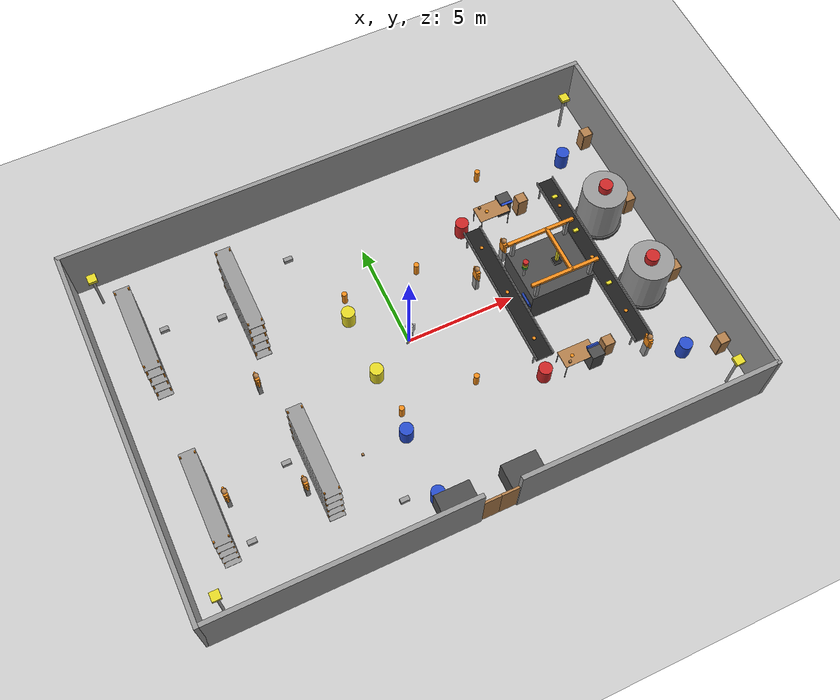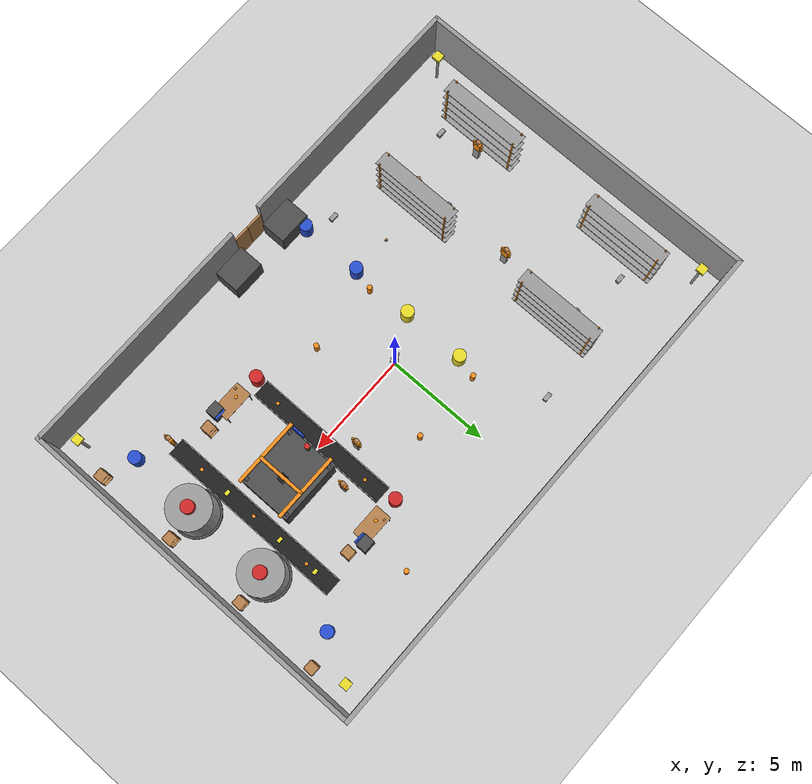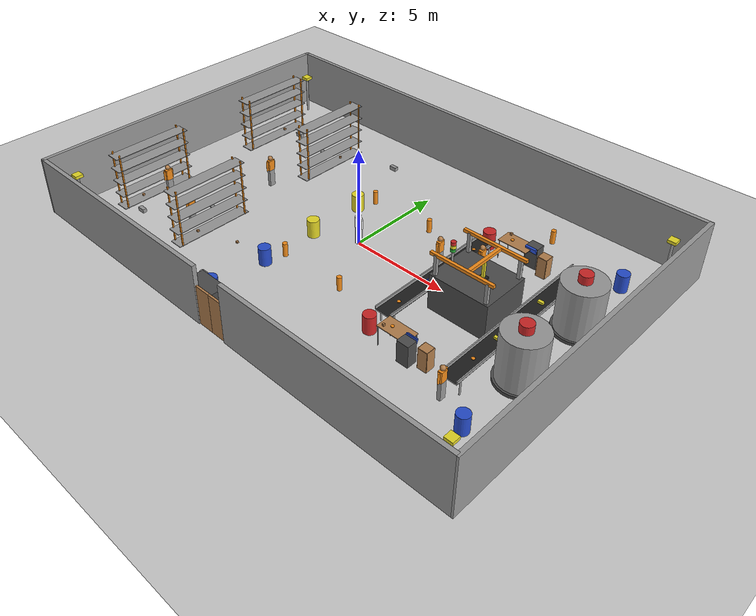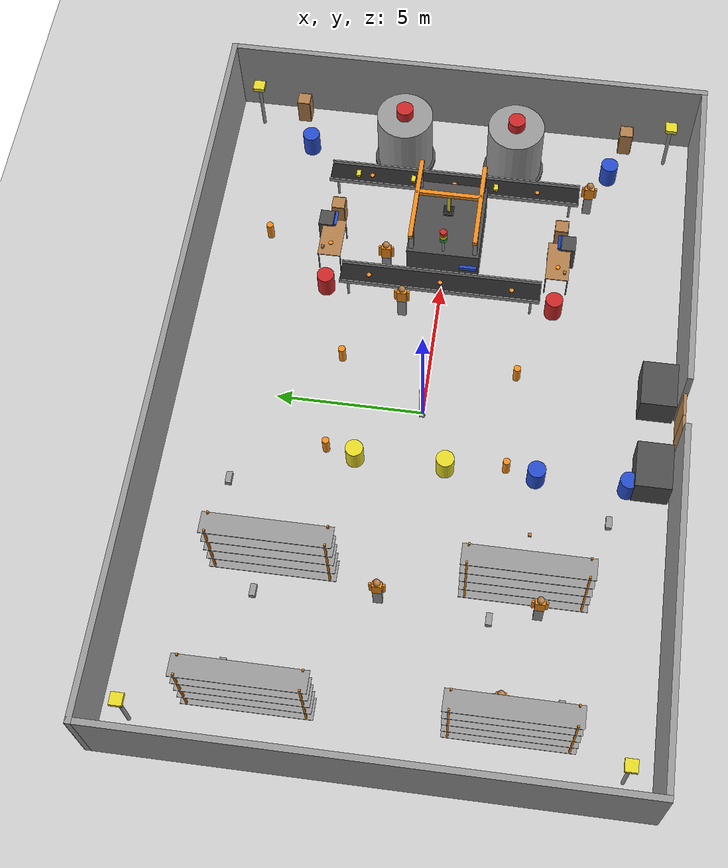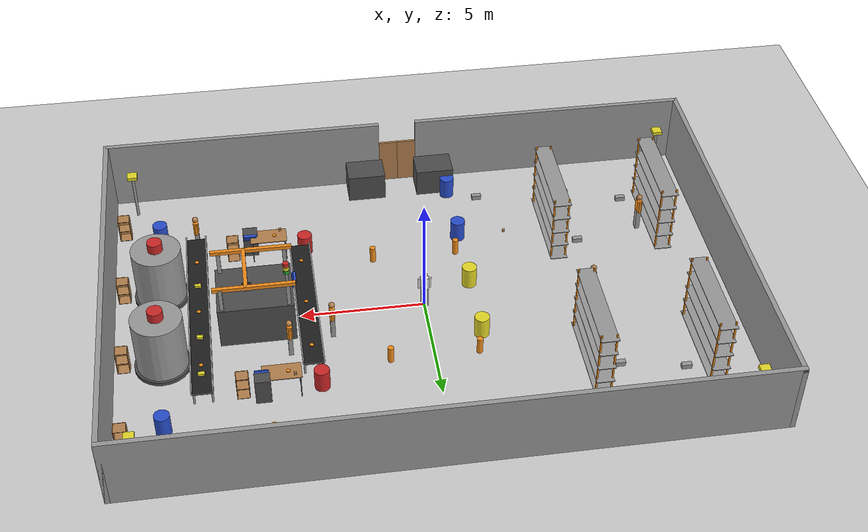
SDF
<sdf version="1.7">
 <world name="default">
  <light name="sun" type="directional">
   <pose>0 0 10 0 -0 0</pose>
   <diffuse>0.8 0.8 0.8 1</diffuse>
   <specular>0.2 0.2 0.2 1</specular>
   <attenuation>
    <range>1000</range>
    <constant>0.9</constant>
    <linear>0.01</linear>
    <quadratic>0.001</quadratic>
   </attenuation>
   <direction>-0.5 0.1 -0.9</direction>
   <spot><inner_angle>0</inner_angle><outer_angle>0</outer_angle><falloff>0</falloff></spot>
  </light>
  <gravity>0 0 -9.8</gravity>
  <magnetic_field>6e-06 2.3e-05 -4.2e-05</magnetic_field>
  <atmosphere type="adiabatic"/>
  <physics type="ode">
   <max_step_size>0.001</max_step_size>
   <real_time_factor>1</real_time_factor>
   <real_time_update_rate>1000</real_time_update_rate>
  </physics>
  <scene><ambient>0.4 0.4 0.4 1</ambient><background>0.7 0.7 0.7 1</background><shadows>1</shadows></scene>
  <audio><device>default</device></audio>
  <spherical_coordinates>
   <surface_model>EARTH_WGS84</surface_model>
   <latitude_deg>0</latitude_deg>
   <longitude_deg>0</longitude_deg>
   <elevation>0</elevation>
   <heading_deg>0</heading_deg>
  </spherical_coordinates>
  <model name="cabinet">
   <static>1</static>
   <link name="cabinet_bottom_plate">
    <inertial>
     <pose>0 0 -1 0 -0 0</pose>
     <inertia><ixx>2.05</ixx><ixy>0</ixy><ixz>0</ixz><iyy>2.05</iyy><iyz>0</iyz><izz>2.05</izz></inertia>
     <mass>25</mass>
    </inertial>
    <collision name="cabinet_bottom_plate_geom">
     <pose>0 0 0.01 0 -0 0</pose>
     <geometry><box><size>0.45 0.45 0.02</size></box></geometry>
    </collision>
    <visual name="cabinet_bottom_plate_geom_visual">
     <pose>0 0 0.01 0 -0 0</pose>
     <geometry><box><size>0.45 0.45 0.02</size></box></geometry>
     <material>
      <script><uri>file://media/materials/scripts/gazebo.material</uri><name>Gazebo/Wood</name></script>
     </material>
    </visual>
    <collision name="cabinet_bottom_plate_geom_cabinet_back_plate">
     <pose>0.235 0 0.51 0 -0 0</pose>
     <geometry><box><size>0.02 0.45 1.02</size></box></geometry>
    </collision>
    <visual name="cabinet_bottom_plate_geom_cabinet_back_plate_visual">
     <pose>0.235 0 0.51 0 -0 0</pose>
     <geometry><box><size>0.02 0.45 1.02</size></box></geometry>
     <material>
      <script><uri>file://media/materials/scripts/gazebo.material</uri><name>Gazebo/Wood</name></script>
     </material>
    </visual>
    <collision name="cabinet_bottom_plate_geom_cabinet_left_plate">
     <pose>0 0.235 0.51 0 -0 0</pose>
     <geometry><box><size>0.45 0.02 1.02</size></box></geometry>
    </collision>
    <visual name="cabinet_bottom_plate_geom_cabinet_left_plate_visual">
     <pose>0 0.235 0.51 0 -0 0</pose>
     <geometry><box><size>0.45 0.02 1.02</size></box></geometry>
     <material>
      <script><uri>file://media/materials/scripts/gazebo.material</uri><name>Gazebo/Wood</name></script>
     </material>
    </visual>
    <collision name="cabinet_bottom_plate_geom_cabinet_middle_plate">
     <pose>0 0 0.51 0 -0 0</pose>
     <geometry><box><size>0.45 0.45 0.02</size></box></geometry>
    </collision>
    <visual name="cabinet_bottom_plate_geom_cabinet_middle_plate_visual">
     <pose>0 0 0.51 0 -0 0</pose>
     <geometry><box><size>0.45 0.45 0.02</size></box></geometry>
     <material>
      <script><uri>file://media/materials/scripts/gazebo.material</uri><name>Gazebo/Wood</name></script>
     </material>
    </visual>
    <collision name="cabinet_bottom_plate_geom_cabinet_right_plate">
     <pose>0 -0.235 0.51 0 -0 0</pose>
     <geometry><box><size>0.45 0.02 1.02</size></box></geometry>
    </collision>
    <visual name="cabinet_bottom_plate_geom_cabinet_right_plate_visual">
     <pose>0 -0.235 0.51 0 -0 0</pose>
     <geometry><box><size>0.45 0.02 1.02</size></box></geometry>
     <material>
      <script><uri>file://media/materials/scripts/gazebo.material</uri><name>Gazebo/Wood</name></script>
     </material>
    </visual>
    <collision name="cabinet_bottom_plate_geom_cabinet_top_plate">
     <pose>0 0 1.01 0 -0 0</pose>
     <geometry><box><size>0.45 0.45 0.02</size></box></geometry>
    </collision>
    <visual name="cabinet_bottom_plate_geom_cabinet_top_plate_visual">
     <pose>0 0 1.01 0 -0 0</pose>
     <geometry><box><size>0.45 0.45 0.02</size></box></geometry>
     <material>
      <script><uri>file://media/materials/scripts/gazebo.material</uri><name>Gazebo/Wood</name></script>
     </material>
    </visual>
   </link>
   <pose>12 -6 0 0 -0 -1.5708</pose>
  </model>
  <model name="cabinet_0">
   <static>1</static>
   <link name="cabinet_bottom_plate">
    <inertial>
     <pose>0 0 -1 0 -0 0</pose>
     <inertia><ixx>2.05</ixx><ixy>0</ixy><ixz>0</ixz><iyy>2.05</iyy><iyz>0</iyz><izz>2.05</izz></inertia>
     <mass>25</mass>
    </inertial>
    <collision name="cabinet_bottom_plate_geom">
     <pose>0 0 0.01 0 -0 0</pose>
     <geometry><box><size>0.45 0.45 0.02</size></box></geometry>
    </collision>
    <visual name="cabinet_bottom_plate_geom_visual">
     <pose>0 0 0.01 0 -0 0</pose>
     <geometry><box><size>0.45 0.45 0.02</size></box></geometry>
     <material>
      <script><uri>file://media/materials/scripts/gazebo.material</uri><name>Gazebo/Wood</name></script>
     </material>
    </visual>
    <collision name="cabinet_bottom_plate_geom_cabinet_back_plate">
     <pose>0.235 0 0.51 0 -0 0</pose>
     <geometry><box><size>0.02 0.45 1.02</size></box></geometry>
    </collision>
    <visual name="cabinet_bottom_plate_geom_cabinet_back_plate_visual">
     <pose>0.235 0 0.51 0 -0 0</pose>
     <geometry><box><size>0.02 0.45 1.02</size></box></geometry>
     <material>
      <script><uri>file://media/materials/scripts/gazebo.material</uri><name>Gazebo/Wood</name></script>
     </material>
    </visual>
    <collision name="cabinet_bottom_plate_geom_cabinet_left_plate">
     <pose>0 0.235 0.51 0 -0 0</pose>
     <geometry><box><size>0.45 0.02 1.02</size></box></geometry>
    </collision>
    <visual name="cabinet_bottom_plate_geom_cabinet_left_plate_visual">
     <pose>0 0.235 0.51 0 -0 0</pose>
     <geometry><box><size>0.45 0.02 1.02</size></box></geometry>
     <material>
      <script><uri>file://media/materials/scripts/gazebo.material</uri><name>Gazebo/Wood</name></script>
     </material>
    </visual>
    <collision name="cabinet_bottom_plate_geom_cabinet_middle_plate">
     <pose>0 0 0.51 0 -0 0</pose>
     <geometry><box><size>0.45 0.45 0.02</size></box></geometry>
    </collision>
    <visual name="cabinet_bottom_plate_geom_cabinet_middle_plate_visual">
     <pose>0 0 0.51 0 -0 0</pose>
     <geometry><box><size>0.45 0.45 0.02</size></box></geometry>
     <material>
      <script><uri>file://media/materials/scripts/gazebo.material</uri><name>Gazebo/Wood</name></script>
     </material>
    </visual>
    <collision name="cabinet_bottom_plate_geom_cabinet_right_plate">
     <pose>0 -0.235 0.51 0 -0 0</pose>
     <geometry><box><size>0.45 0.02 1.02</size></box></geometry>
    </collision>
    <visual name="cabinet_bottom_plate_geom_cabinet_right_plate_visual">
     <pose>0 -0.235 0.51 0 -0 0</pose>
     <geometry><box><size>0.45 0.02 1.02</size></box></geometry>
     <material>
      <script><uri>file://media/materials/scripts/gazebo.material</uri><name>Gazebo/Wood</name></script>
     </material>
    </visual>
    <collision name="cabinet_bottom_plate_geom_cabinet_top_plate">
     <pose>0 0 1.01 0 -0 0</pose>
     <geometry><box><size>0.45 0.45 0.02</size></box></geometry>
    </collision>
    <visual name="cabinet_bottom_plate_geom_cabinet_top_plate_visual">
     <pose>0 0 1.01 0 -0 0</pose>
     <geometry><box><size>0.45 0.45 0.02</size></box></geometry>
     <material>
      <script><uri>file://media/materials/scripts/gazebo.material</uri><name>Gazebo/Wood</name></script>
     </material>
    </visual>
   </link>
   <pose>12 -2 0 0 -0 -1.5708</pose>
  </model>
  <model name="ground_plane">
   <static>1</static>
   <link name="link">
    <collision name="collision">
     <geometry><plane><normal>0 0 1</normal><size>100 100</size></plane></geometry>
     <surface><friction><ode><mu>100</mu><mu2>50</mu2></ode></friction></surface>
    </collision>
    <visual name="visual">
     <cast_shadows>0</cast_shadows>
     <geometry><plane><normal>0 0 1</normal><size>100 100</size></plane></geometry>
     <material>
      <script><uri>file://media/materials/scripts/gazebo.material</uri><name>Gazebo/Grey</name></script>
     </material>
    </visual>
   </link>
  </model>
  <model name="table">
   <static>1</static>
   <link name="link">
    <collision name="surface">
     <pose>0 0 1 0 -0 0</pose>
     <geometry><box><size>1.5 0.8 0.03</size></box></geometry>
     <surface><friction><ode><mu>0.6</mu><mu2>0.6</mu2></ode></friction></surface>
    </collision>
    <visual name="visual1">
     <pose>0 0 1 0 -0 0</pose>
     <geometry><box><size>1.5 0.8 0.03</size></box></geometry>
     <material>
      <script><uri>file://media/materials/scripts/gazebo.material</uri><name>Gazebo/Wood</name></script>
     </material>
    </visual>
    <collision name="front_left_leg">
     <pose>0.68 0.38 0.5 0 -0 0</pose>
     <geometry><cylinder><radius>0.02</radius><length>1</length></cylinder></geometry>
    </collision>
    <visual name="front_left_leg_visual2">
     <pose>0.68 0.38 0.5 0 -0 0</pose>
     <geometry><cylinder><radius>0.02</radius><length>1</length></cylinder></geometry>
     <material>
      <script><uri>file://media/materials/scripts/gazebo.material</uri><name>Gazebo/Grey</name></script>
     </material>
    </visual>
    <collision name="front_right_leg">
     <pose>0.68 -0.38 0.5 0 -0 0</pose>
     <geometry><cylinder><radius>0.02</radius><length>1</length></cylinder></geometry>
    </collision>
    <visual name="front_right_leg_visual2">
     <pose>0.68 -0.38 0.5 0 -0 0</pose>
     <geometry><cylinder><radius>0.02</radius><length>1</length></cylinder></geometry>
     <material>
      <script><uri>file://media/materials/scripts/gazebo.material</uri><name>Gazebo/Grey</name></script>
     </material>
    </visual>
    <collision name="back_right_leg">
     <pose>-0.68 -0.38 0.5 0 -0 0</pose>
     <geometry><cylinder><radius>0.02</radius><length>1</length></cylinder></geometry>
    </collision>
    <visual name="back_right_leg_visual2">
     <pose>-0.68 -0.38 0.5 0 -0 0</pose>
     <geometry><cylinder><radius>0.02</radius><length>1</length></cylinder></geometry>
     <material>
      <script><uri>file://media/materials/scripts/gazebo.material</uri><name>Gazebo/Grey</name></script>
     </material>
    </visual>
    <collision name="back_left_leg">
     <pose>-0.68 0.38 0.5 0 -0 0</pose>
     <geometry><cylinder><radius>0.02</radius><length>1</length></cylinder></geometry>
    </collision>
    <visual name="back_left_leg_visual2">
     <pose>-0.68 0.38 0.5 0 -0 0</pose>
     <geometry><cylinder><radius>0.02</radius><length>1</length></cylinder></geometry>
     <material>
      <script><uri>file://media/materials/scripts/gazebo.material</uri><name>Gazebo/Grey</name></script>
     </material>
    </visual>
   </link>
   <pose>6 -4 0 0 -0 0</pose>
  </model>
  <model name="wood_cube_10cm">
   <link name="link">
    <pose>0 0 0.05 0 -0 0</pose>
    <inertial>
     <mass>0.5167</mass>
     <inertia>
      <ixx>0.000861167</ixx>
      <ixy>0</ixy>
      <ixz>0</ixz>
      <iyy>0.000861167</iyy>
      <iyz>0</iyz>
      <izz>0.000861167</izz>
     </inertia>
    </inertial>
    <collision name="collision">
     <geometry><box><size>0.1 0.1 0.1</size></box></geometry>
     <surface>
      <contact>
       <poissons_ratio>0.347</poissons_ratio>
       <elastic_modulus>8.8e+09</elastic_modulus>
       <ode><kp>100000</kp><kd>100</kd><max_vel>100</max_vel><min_depth>0.001</min_depth></ode>
      </contact>
      <friction>
       <torsional>
        <coefficient>1</coefficient>
        <use_patch_radius>0</use_patch_radius>
        <surface_radius>0.01</surface_radius>
       </torsional>
      </friction>
     </surface>
    </collision>
    <visual name="visual">
     <geometry><box><size>0.1 0.1 0.1</size></box></geometry>
     <material>
      <script><uri>file://media/materials/scripts/gazebo.material</uri><name>Gazebo/Wood</name></script>
     </material>
    </visual>
   </link>
   <pose>-4 -4 0.08 0 -0 0</pose>
  </model>
  <model name="door_08x2m">
   <link name="link">
    <visual name="visual">
     <geometry><box><size>0.1 0.8 2</size></box></geometry>
     <material>
      <script><uri>file://media/materials/scripts/gazebo.material</uri><name>Gazebo/Wood</name></script>
     </material>
    </visual>
   </link>
   <static>1</static>
   <pose>-0.4 -8.5 1 0 -0 1.5708</pose>
  </model>
  <model name="door_08x2m_clone">
   <link name="link">
    <visual name="visual">
     <geometry><box><size>0.1 0.8 2</size></box></geometry>
     <material>
      <script><uri>file://media/materials/scripts/gazebo.material</uri><name>Gazebo/Wood</name></script>
     </material>
    </visual>
   </link>
   <static>1</static>
   <pose>0.4 -8.5 1 0 -0 1.5708</pose>
  </model>
  <model name="table_2">
   <static>1</static>
   <link name="link">
    <collision name="surface">
     <pose>0 0 1 0 -0 0</pose>
     <geometry><box><size>1.5 0.8 0.03</size></box></geometry>
     <surface><friction><ode><mu>0.6</mu><mu2>0.6</mu2></ode></friction></surface>
    </collision>
    <visual name="visual1">
     <pose>0 0 1 0 -0 0</pose>
     <geometry><box><size>1.5 0.8 0.03</size></box></geometry>
     <material>
      <script><uri>file://media/materials/scripts/gazebo.material</uri><name>Gazebo/Wood</name></script>
     </material>
    </visual>
    <collision name="front_left_leg">
     <pose>0.68 0.38 0.5 0 -0 0</pose>
     <geometry><cylinder><radius>0.02</radius><length>1</length></cylinder></geometry>
    </collision>
    <visual name="front_left_leg_visual2">
     <pose>0.68 0.38 0.5 0 -0 0</pose>
     <geometry><cylinder><radius>0.02</radius><length>1</length></cylinder></geometry>
     <material>
      <script><uri>file://media/materials/scripts/gazebo.material</uri><name>Gazebo/Grey</name></script>
     </material>
    </visual>
    <collision name="front_right_leg">
     <pose>0.68 -0.38 0.5 0 -0 0</pose>
     <geometry><cylinder><radius>0.02</radius><length>1</length></cylinder></geometry>
    </collision>
    <visual name="front_right_leg_visual2">
     <pose>0.68 -0.38 0.5 0 -0 0</pose>
     <geometry><cylinder><radius>0.02</radius><length>1</length></cylinder></geometry>
     <material>
      <script><uri>file://media/materials/scripts/gazebo.material</uri><name>Gazebo/Grey</name></script>
     </material>
    </visual>
    <collision name="back_right_leg">
     <pose>-0.68 -0.38 0.5 0 -0 0</pose>
     <geometry><cylinder><radius>0.02</radius><length>1</length></cylinder></geometry>
    </collision>
    <visual name="back_right_leg_visual2">
     <pose>-0.68 -0.38 0.5 0 -0 0</pose>
     <geometry><cylinder><radius>0.02</radius><length>1</length></cylinder></geometry>
     <material>
      <script><uri>file://media/materials/scripts/gazebo.material</uri><name>Gazebo/Grey</name></script>
     </material>
    </visual>
    <collision name="back_left_leg">
     <pose>-0.68 0.38 0.5 0 -0 0</pose>
     <geometry><cylinder><radius>0.02</radius><length>1</length></cylinder></geometry>
    </collision>
    <visual name="back_left_leg_visual2">
     <pose>-0.68 0.38 0.5 0 -0 0</pose>
     <geometry><cylinder><radius>0.02</radius><length>1</length></cylinder></geometry>
     <material>
      <script><uri>file://media/materials/scripts/gazebo.material</uri><name>Gazebo/Grey</name></script>
     </material>
    </visual>
   </link>
   <pose>6 4 0 0 -0 0</pose>
  </model>
  <model name="cabinet_1">
   <static>1</static>
   <link name="cabinet_bottom_plate">
    <inertial>
     <pose>0 0 -1 0 -0 0</pose>
     <inertia><ixx>2.05</ixx><ixy>0</ixy><ixz>0</ixz><iyy>2.05</iyy><iyz>0</iyz><izz>2.05</izz></inertia>
     <mass>25</mass>
    </inertial>
    <collision name="cabinet_bottom_plate_geom">
     <pose>0 0 0.01 0 -0 0</pose>
     <geometry><box><size>0.45 0.45 0.02</size></box></geometry>
    </collision>
    <visual name="cabinet_bottom_plate_geom_visual">
     <pose>0 0 0.01 0 -0 0</pose>
     <geometry><box><size>0.45 0.45 0.02</size></box></geometry>
     <material>
      <script><uri>file://media/materials/scripts/gazebo.material</uri><name>Gazebo/Wood</name></script>
     </material>
    </visual>
    <collision name="cabinet_bottom_plate_geom_cabinet_back_plate">
     <pose>0.235 0 0.51 0 -0 0</pose>
     <geometry><box><size>0.02 0.45 1.02</size></box></geometry>
    </collision>
    <visual name="cabinet_bottom_plate_geom_cabinet_back_plate_visual">
     <pose>0.235 0 0.51 0 -0 0</pose>
     <geometry><box><size>0.02 0.45 1.02</size></box></geometry>
     <material>
      <script><uri>file://media/materials/scripts/gazebo.material</uri><name>Gazebo/Wood</name></script>
     </material>
    </visual>
    <collision name="cabinet_bottom_plate_geom_cabinet_left_plate">
     <pose>0 0.235 0.51 0 -0 0</pose>
     <geometry><box><size>0.45 0.02 1.02</size></box></geometry>
    </collision>
    <visual name="cabinet_bottom_plate_geom_cabinet_left_plate_visual">
     <pose>0 0.235 0.51 0 -0 0</pose>
     <geometry><box><size>0.45 0.02 1.02</size></box></geometry>
     <material>
      <script><uri>file://media/materials/scripts/gazebo.material</uri><name>Gazebo/Wood</name></script>
     </material>
    </visual>
    <collision name="cabinet_bottom_plate_geom_cabinet_middle_plate">
     <pose>0 0 0.51 0 -0 0</pose>
     <geometry><box><size>0.45 0.45 0.02</size></box></geometry>
    </collision>
    <visual name="cabinet_bottom_plate_geom_cabinet_middle_plate_visual">
     <pose>0 0 0.51 0 -0 0</pose>
     <geometry><box><size>0.45 0.45 0.02</size></box></geometry>
     <material>
      <script><uri>file://media/materials/scripts/gazebo.material</uri><name>Gazebo/Wood</name></script>
     </material>
    </visual>
    <collision name="cabinet_bottom_plate_geom_cabinet_right_plate">
     <pose>0 -0.235 0.51 0 -0 0</pose>
     <geometry><box><size>0.45 0.02 1.02</size></box></geometry>
    </collision>
    <visual name="cabinet_bottom_plate_geom_cabinet_right_plate_visual">
     <pose>0 -0.235 0.51 0 -0 0</pose>
     <geometry><box><size>0.45 0.02 1.02</size></box></geometry>
     <material>
      <script><uri>file://media/materials/scripts/gazebo.material</uri><name>Gazebo/Wood</name></script>
     </material>
    </visual>
    <collision name="cabinet_bottom_plate_geom_cabinet_top_plate">
     <pose>0 0 1.01 0 -0 0</pose>
     <geometry><box><size>0.45 0.45 0.02</size></box></geometry>
    </collision>
    <visual name="cabinet_bottom_plate_geom_cabinet_top_plate_visual">
     <pose>0 0 1.01 0 -0 0</pose>
     <geometry><box><size>0.45 0.45 0.02</size></box></geometry>
     <material>
      <script><uri>file://media/materials/scripts/gazebo.material</uri><name>Gazebo/Wood</name></script>
     </material>
    </visual>
   </link>
   <pose>12 2 0 0 -0 -1.5708</pose>
  </model>
  <model name="cabinet_2">
   <static>1</static>
   <link name="cabinet_bottom_plate">
    <inertial>
     <pose>0 0 -1 0 -0 0</pose>
     <inertia><ixx>2.05</ixx><ixy>0</ixy><ixz>0</ixz><iyy>2.05</iyy><iyz>0</iyz><izz>2.05</izz></inertia>
     <mass>25</mass>
    </inertial>
    <collision name="cabinet_bottom_plate_geom">
     <pose>0 0 0.01 0 -0 0</pose>
     <geometry><box><size>0.45 0.45 0.02</size></box></geometry>
    </collision>
    <visual name="cabinet_bottom_plate_geom_visual">
     <pose>0 0 0.01 0 -0 0</pose>
     <geometry><box><size>0.45 0.45 0.02</size></box></geometry>
     <material>
      <script><uri>file://media/materials/scripts/gazebo.material</uri><name>Gazebo/Wood</name></script>
     </material>
    </visual>
    <collision name="cabinet_bottom_plate_geom_cabinet_back_plate">
     <pose>0.235 0 0.51 0 -0 0</pose>
     <geometry><box><size>0.02 0.45 1.02</size></box></geometry>
    </collision>
    <visual name="cabinet_bottom_plate_geom_cabinet_back_plate_visual">
     <pose>0.235 0 0.51 0 -0 0</pose>
     <geometry><box><size>0.02 0.45 1.02</size></box></geometry>
     <material>
      <script><uri>file://media/materials/scripts/gazebo.material</uri><name>Gazebo/Wood</name></script>
     </material>
    </visual>
    <collision name="cabinet_bottom_plate_geom_cabinet_left_plate">
     <pose>0 0.235 0.51 0 -0 0</pose>
     <geometry><box><size>0.45 0.02 1.02</size></box></geometry>
    </collision>
    <visual name="cabinet_bottom_plate_geom_cabinet_left_plate_visual">
     <pose>0 0.235 0.51 0 -0 0</pose>
     <geometry><box><size>0.45 0.02 1.02</size></box></geometry>
     <material>
      <script><uri>file://media/materials/scripts/gazebo.material</uri><name>Gazebo/Wood</name></script>
     </material>
    </visual>
    <collision name="cabinet_bottom_plate_geom_cabinet_middle_plate">
     <pose>0 0 0.51 0 -0 0</pose>
     <geometry><box><size>0.45 0.45 0.02</size></box></geometry>
    </collision>
    <visual name="cabinet_bottom_plate_geom_cabinet_middle_plate_visual">
     <pose>0 0 0.51 0 -0 0</pose>
     <geometry><box><size>0.45 0.45 0.02</size></box></geometry>
     <material>
      <script><uri>file://media/materials/scripts/gazebo.material</uri><name>Gazebo/Wood</name></script>
     </material>
    </visual>
    <collision name="cabinet_bottom_plate_geom_cabinet_right_plate">
     <pose>0 -0.235 0.51 0 -0 0</pose>
     <geometry><box><size>0.45 0.02 1.02</size></box></geometry>
    </collision>
    <visual name="cabinet_bottom_plate_geom_cabinet_right_plate_visual">
     <pose>0 -0.235 0.51 0 -0 0</pose>
     <geometry><box><size>0.45 0.02 1.02</size></box></geometry>
     <material>
      <script><uri>file://media/materials/scripts/gazebo.material</uri><name>Gazebo/Wood</name></script>
     </material>
    </visual>
    <collision name="cabinet_bottom_plate_geom_cabinet_top_plate">
     <pose>0 0 1.01 0 -0 0</pose>
     <geometry><box><size>0.45 0.45 0.02</size></box></geometry>
    </collision>
    <visual name="cabinet_bottom_plate_geom_cabinet_top_plate_visual">
     <pose>0 0 1.01 0 -0 0</pose>
     <geometry><box><size>0.45 0.45 0.02</size></box></geometry>
     <material>
      <script><uri>file://media/materials/scripts/gazebo.material</uri><name>Gazebo/Wood</name></script>
     </material>
    </visual>
   </link>
   <pose>12 6 0 0 -0 -1.5708</pose>
  </model>
  <model name="wall_north">
   <static>1</static>
   <link name="link">
    <collision name="box_collision"><geometry><box><size>25.2 0.2 3</size></box></geometry></collision>
    <visual name="box_visual">
     <geometry><box><size>25.2 0.2 3</size></box></geometry>
     <material>
      <script><uri>file://media/materials/scripts/gazebo.material</uri><name>Gazebo/Grey</name></script>
     </material>
    </visual>
   </link>
   <pose>0 8.5 1.5 0 -0 0</pose>
  </model>
  <model name="wall_south_west">
   <static>1</static>
   <link name="link">
    <collision name="box_collision"><geometry><box><size>11.7 0.2 3</size></box></geometry></collision>
    <visual name="box_visual">
     <geometry><box><size>11.7 0.2 3</size></box></geometry>
     <material>
      <script><uri>file://media/materials/scripts/gazebo.material</uri><name>Gazebo/Grey</name></script>
     </material>
    </visual>
   </link>
   <pose>-6.65 -8.5 1.5 0 -0 0</pose>
  </model>
  <model name="wall_south_east">
   <static>1</static>
   <link name="link">
    <collision name="box_collision"><geometry><box><size>11.7 0.2 3</size></box></geometry></collision>
    <visual name="box_visual">
     <geometry><box><size>11.7 0.2 3</size></box></geometry>
     <material>
      <script><uri>file://media/materials/scripts/gazebo.material</uri><name>Gazebo/Grey</name></script>
     </material>
    </visual>
   </link>
   <pose>6.65 -8.5 1.5 0 -0 0</pose>
  </model>
  <model name="wall_east">
   <static>1</static>
   <link name="link">
    <collision name="box_collision"><geometry><box><size>0.2 17.2 3</size></box></geometry></collision>
    <visual name="box_visual">
     <geometry><box><size>0.2 17.2 3</size></box></geometry>
     <material>
      <script><uri>file://media/materials/scripts/gazebo.material</uri><name>Gazebo/Grey</name></script>
     </material>
    </visual>
   </link>
   <pose>12.5 0 1.5 0 -0 0</pose>
  </model>
  <model name="wall_west">
   <static>1</static>
   <link name="link">
    <collision name="box_collision"><geometry><box><size>0.2 17.2 3</size></box></geometry></collision>
    <visual name="box_visual">
     <geometry><box><size>0.2 17.2 3</size></box></geometry>
     <material>
      <script><uri>file://media/materials/scripts/gazebo.material</uri><name>Gazebo/Grey</name></script>
     </material>
    </visual>
   </link>
   <pose>-12.5 0 1.5 0 -0 0</pose>
  </model>
  <model name="shelf_rack_a">
   <static>1</static>
   <link name="frame">
    <collision name="post0_collision">
     <geometry><box><size>0.06 0.06 3</size></box></geometry>
     <pose>-0.3 -1.85 1.5 0 -0 0</pose>
    </collision>
    <visual name="post0_visual">
     <geometry><box><size>0.06 0.06 3</size></box></geometry>
     <pose>-0.3 -1.85 1.5 0 -0 0</pose>
     <material>
      <script><uri>file://media/materials/scripts/gazebo.material</uri><name>Gazebo/Orange</name></script>
     </material>
    </visual>
    <collision name="post1_collision">
     <geometry><box><size>0.06 0.06 3</size></box></geometry>
     <pose>0.3 -1.85 1.5 0 -0 0</pose>
    </collision>
    <visual name="post1_visual">
     <geometry><box><size>0.06 0.06 3</size></box></geometry>
     <pose>0.3 -1.85 1.5 0 -0 0</pose>
     <material>
      <script><uri>file://media/materials/scripts/gazebo.material</uri><name>Gazebo/Orange</name></script>
     </material>
    </visual>
    <collision name="post2_collision">
     <geometry><box><size>0.06 0.06 3</size></box></geometry>
     <pose>-0.3 1.85 1.5 0 -0 0</pose>
    </collision>
    <visual name="post2_visual">
     <geometry><box><size>0.06 0.06 3</size></box></geometry>
     <pose>-0.3 1.85 1.5 0 -0 0</pose>
     <material>
      <script><uri>file://media/materials/scripts/gazebo.material</uri><name>Gazebo/Orange</name></script>
     </material>
    </visual>
    <collision name="post3_collision">
     <geometry><box><size>0.06 0.06 3</size></box></geometry>
     <pose>0.3 1.85 1.5 0 -0 0</pose>
    </collision>
    <visual name="post3_visual">
     <geometry><box><size>0.06 0.06 3</size></box></geometry>
     <pose>0.3 1.85 1.5 0 -0 0</pose>
     <material>
      <script><uri>file://media/materials/scripts/gazebo.material</uri><name>Gazebo/Orange</name></script>
     </material>
    </visual>
    <collision name="shelf0_collision">
     <geometry><box><size>0.7 4.1 0.03</size></box></geometry>
     <pose>0 0 0.05 0 -0 0</pose>
    </collision>
    <visual name="shelf0_visual">
     <geometry><box><size>0.7 4.1 0.03</size></box></geometry>
     <pose>0 0 0.05 0 -0 0</pose>
     <material>
      <script><uri>file://media/materials/scripts/gazebo.material</uri><name>Gazebo/Grey</name></script>
     </material>
    </visual>
    <collision name="shelf1_collision">
     <geometry><box><size>0.7 4.1 0.03</size></box></geometry>
     <pose>0 0 0.75 0 -0 0</pose>
    </collision>
    <visual name="shelf1_visual">
     <geometry><box><size>0.7 4.1 0.03</size></box></geometry>
     <pose>0 0 0.75 0 -0 0</pose>
     <material>
      <script><uri>file://media/materials/scripts/gazebo.material</uri><name>Gazebo/Grey</name></script>
     </material>
    </visual>
    <collision name="shelf2_collision">
     <geometry><box><size>0.7 4.1 0.03</size></box></geometry>
     <pose>0 0 1.45 0 -0 0</pose>
    </collision>
    <visual name="shelf2_visual">
     <geometry><box><size>0.7 4.1 0.03</size></box></geometry>
     <pose>0 0 1.45 0 -0 0</pose>
     <material>
      <script><uri>file://media/materials/scripts/gazebo.material</uri><name>Gazebo/Grey</name></script>
     </material>
    </visual>
    <collision name="shelf3_collision">
     <geometry><box><size>0.7 4.1 0.03</size></box></geometry>
     <pose>0 0 2.15 0 -0 0</pose>
    </collision>
    <visual name="shelf3_visual">
     <geometry><box><size>0.7 4.1 0.03</size></box></geometry>
     <pose>0 0 2.15 0 -0 0</pose>
     <material>
      <script><uri>file://media/materials/scripts/gazebo.material</uri><name>Gazebo/Grey</name></script>
     </material>
    </visual>
    <collision name="shelf4_collision">
     <geometry><box><size>0.7 4.1 0.03</size></box></geometry>
     <pose>0 0 2.85 0 -0 0</pose>
    </collision>
    <visual name="shelf4_visual">
     <geometry><box><size>0.7 4.1 0.03</size></box></geometry>
     <pose>0 0 2.85 0 -0 0</pose>
     <material>
      <script><uri>file://media/materials/scripts/gazebo.material</uri><name>Gazebo/Grey</name></script>
     </material>
    </visual>
   </link>
   <pose>-10.5 -4 0 0 -0 0</pose>
  </model>
  <model name="shelf_rack_b">
   <static>1</static>
   <link name="frame">
    <collision name="post0_collision">
     <geometry><box><size>0.06 0.06 3</size></box></geometry>
     <pose>-0.3 -1.85 1.5 0 -0 0</pose>
    </collision>
    <visual name="post0_visual">
     <geometry><box><size>0.06 0.06 3</size></box></geometry>
     <pose>-0.3 -1.85 1.5 0 -0 0</pose>
     <material>
      <script><uri>file://media/materials/scripts/gazebo.material</uri><name>Gazebo/Orange</name></script>
     </material>
    </visual>
    <collision name="post1_collision">
     <geometry><box><size>0.06 0.06 3</size></box></geometry>
     <pose>0.3 -1.85 1.5 0 -0 0</pose>
    </collision>
    <visual name="post1_visual">
     <geometry><box><size>0.06 0.06 3</size></box></geometry>
     <pose>0.3 -1.85 1.5 0 -0 0</pose>
     <material>
      <script><uri>file://media/materials/scripts/gazebo.material</uri><name>Gazebo/Orange</name></script>
     </material>
    </visual>
    <collision name="post2_collision">
     <geometry><box><size>0.06 0.06 3</size></box></geometry>
     <pose>-0.3 1.85 1.5 0 -0 0</pose>
    </collision>
    <visual name="post2_visual">
     <geometry><box><size>0.06 0.06 3</size></box></geometry>
     <pose>-0.3 1.85 1.5 0 -0 0</pose>
     <material>
      <script><uri>file://media/materials/scripts/gazebo.material</uri><name>Gazebo/Orange</name></script>
     </material>
    </visual>
    <collision name="post3_collision">
     <geometry><box><size>0.06 0.06 3</size></box></geometry>
     <pose>0.3 1.85 1.5 0 -0 0</pose>
    </collision>
    <visual name="post3_visual">
     <geometry><box><size>0.06 0.06 3</size></box></geometry>
     <pose>0.3 1.85 1.5 0 -0 0</pose>
     <material>
      <script><uri>file://media/materials/scripts/gazebo.material</uri><name>Gazebo/Orange</name></script>
     </material>
    </visual>
    <collision name="shelf0_collision">
     <geometry><box><size>0.7 4.1 0.03</size></box></geometry>
     <pose>0 0 0.05 0 -0 0</pose>
    </collision>
    <visual name="shelf0_visual">
     <geometry><box><size>0.7 4.1 0.03</size></box></geometry>
     <pose>0 0 0.05 0 -0 0</pose>
     <material>
      <script><uri>file://media/materials/scripts/gazebo.material</uri><name>Gazebo/Grey</name></script>
     </material>
    </visual>
    <collision name="shelf1_collision">
     <geometry><box><size>0.7 4.1 0.03</size></box></geometry>
     <pose>0 0 0.75 0 -0 0</pose>
    </collision>
    <visual name="shelf1_visual">
     <geometry><box><size>0.7 4.1 0.03</size></box></geometry>
     <pose>0 0 0.75 0 -0 0</pose>
     <material>
      <script><uri>file://media/materials/scripts/gazebo.material</uri><name>Gazebo/Grey</name></script>
     </material>
    </visual>
    <collision name="shelf2_collision">
     <geometry><box><size>0.7 4.1 0.03</size></box></geometry>
     <pose>0 0 1.45 0 -0 0</pose>
    </collision>
    <visual name="shelf2_visual">
     <geometry><box><size>0.7 4.1 0.03</size></box></geometry>
     <pose>0 0 1.45 0 -0 0</pose>
     <material>
      <script><uri>file://media/materials/scripts/gazebo.material</uri><name>Gazebo/Grey</name></script>
     </material>
    </visual>
    <collision name="shelf3_collision">
     <geometry><box><size>0.7 4.1 0.03</size></box></geometry>
     <pose>0 0 2.15 0 -0 0</pose>
    </collision>
    <visual name="shelf3_visual">
     <geometry><box><size>0.7 4.1 0.03</size></box></geometry>
     <pose>0 0 2.15 0 -0 0</pose>
     <material>
      <script><uri>file://media/materials/scripts/gazebo.material</uri><name>Gazebo/Grey</name></script>
     </material>
    </visual>
    <collision name="shelf4_collision">
     <geometry><box><size>0.7 4.1 0.03</size></box></geometry>
     <pose>0 0 2.85 0 -0 0</pose>
    </collision>
    <visual name="shelf4_visual">
     <geometry><box><size>0.7 4.1 0.03</size></box></geometry>
     <pose>0 0 2.85 0 -0 0</pose>
     <material>
      <script><uri>file://media/materials/scripts/gazebo.material</uri><name>Gazebo/Grey</name></script>
     </material>
    </visual>
   </link>
   <pose>-10.5 4 0 0 -0 0</pose>
  </model>
  <model name="shelf_rack_c">
   <static>1</static>
   <link name="frame">
    <collision name="post0_collision">
     <geometry><box><size>0.06 0.06 3</size></box></geometry>
     <pose>-0.3 -1.85 1.5 0 -0 0</pose>
    </collision>
    <visual name="post0_visual">
     <geometry><box><size>0.06 0.06 3</size></box></geometry>
     <pose>-0.3 -1.85 1.5 0 -0 0</pose>
     <material>
      <script><uri>file://media/materials/scripts/gazebo.material</uri><name>Gazebo/Orange</name></script>
     </material>
    </visual>
    <collision name="post1_collision">
     <geometry><box><size>0.06 0.06 3</size></box></geometry>
     <pose>0.3 -1.85 1.5 0 -0 0</pose>
    </collision>
    <visual name="post1_visual">
     <geometry><box><size>0.06 0.06 3</size></box></geometry>
     <pose>0.3 -1.85 1.5 0 -0 0</pose>
     <material>
      <script><uri>file://media/materials/scripts/gazebo.material</uri><name>Gazebo/Orange</name></script>
     </material>
    </visual>
    <collision name="post2_collision">
     <geometry><box><size>0.06 0.06 3</size></box></geometry>
     <pose>-0.3 1.85 1.5 0 -0 0</pose>
    </collision>
    <visual name="post2_visual">
     <geometry><box><size>0.06 0.06 3</size></box></geometry>
     <pose>-0.3 1.85 1.5 0 -0 0</pose>
     <material>
      <script><uri>file://media/materials/scripts/gazebo.material</uri><name>Gazebo/Orange</name></script>
     </material>
    </visual>
    <collision name="post3_collision">
     <geometry><box><size>0.06 0.06 3</size></box></geometry>
     <pose>0.3 1.85 1.5 0 -0 0</pose>
    </collision>
    <visual name="post3_visual">
     <geometry><box><size>0.06 0.06 3</size></box></geometry>
     <pose>0.3 1.85 1.5 0 -0 0</pose>
     <material>
      <script><uri>file://media/materials/scripts/gazebo.material</uri><name>Gazebo/Orange</name></script>
     </material>
    </visual>
    <collision name="shelf0_collision">
     <geometry><box><size>0.7 4.1 0.03</size></box></geometry>
     <pose>0 0 0.05 0 -0 0</pose>
    </collision>
    <visual name="shelf0_visual">
     <geometry><box><size>0.7 4.1 0.03</size></box></geometry>
     <pose>0 0 0.05 0 -0 0</pose>
     <material>
      <script><uri>file://media/materials/scripts/gazebo.material</uri><name>Gazebo/Grey</name></script>
     </material>
    </visual>
    <collision name="shelf1_collision">
     <geometry><box><size>0.7 4.1 0.03</size></box></geometry>
     <pose>0 0 0.75 0 -0 0</pose>
    </collision>
    <visual name="shelf1_visual">
     <geometry><box><size>0.7 4.1 0.03</size></box></geometry>
     <pose>0 0 0.75 0 -0 0</pose>
     <material>
      <script><uri>file://media/materials/scripts/gazebo.material</uri><name>Gazebo/Grey</name></script>
     </material>
    </visual>
    <collision name="shelf2_collision">
     <geometry><box><size>0.7 4.1 0.03</size></box></geometry>
     <pose>0 0 1.45 0 -0 0</pose>
    </collision>
    <visual name="shelf2_visual">
     <geometry><box><size>0.7 4.1 0.03</size></box></geometry>
     <pose>0 0 1.45 0 -0 0</pose>
     <material>
      <script><uri>file://media/materials/scripts/gazebo.material</uri><name>Gazebo/Grey</name></script>
     </material>
    </visual>
    <collision name="shelf3_collision">
     <geometry><box><size>0.7 4.1 0.03</size></box></geometry>
     <pose>0 0 2.15 0 -0 0</pose>
    </collision>
    <visual name="shelf3_visual">
     <geometry><box><size>0.7 4.1 0.03</size></box></geometry>
     <pose>0 0 2.15 0 -0 0</pose>
     <material>
      <script><uri>file://media/materials/scripts/gazebo.material</uri><name>Gazebo/Grey</name></script>
     </material>
    </visual>
    <collision name="shelf4_collision">
     <geometry><box><size>0.7 4.1 0.03</size></box></geometry>
     <pose>0 0 2.85 0 -0 0</pose>
    </collision>
    <visual name="shelf4_visual">
     <geometry><box><size>0.7 4.1 0.03</size></box></geometry>
     <pose>0 0 2.85 0 -0 0</pose>
     <material>
      <script><uri>file://media/materials/scripts/gazebo.material</uri><name>Gazebo/Grey</name></script>
     </material>
    </visual>
   </link>
   <pose>-6 -4 0 0 -0 0</pose>
  </model>
  <model name="shelf_rack_d">
   <static>1</static>
   <link name="frame">
    <collision name="post0_collision">
     <geometry><box><size>0.06 0.06 3</size></box></geometry>
     <pose>-0.3 -1.85 1.5 0 -0 0</pose>
    </collision>
    <visual name="post0_visual">
     <geometry><box><size>0.06 0.06 3</size></box></geometry>
     <pose>-0.3 -1.85 1.5 0 -0 0</pose>
     <material>
      <script><uri>file://media/materials/scripts/gazebo.material</uri><name>Gazebo/Orange</name></script>
     </material>
    </visual>
    <collision name="post1_collision">
     <geometry><box><size>0.06 0.06 3</size></box></geometry>
     <pose>0.3 -1.85 1.5 0 -0 0</pose>
    </collision>
    <visual name="post1_visual">
     <geometry><box><size>0.06 0.06 3</size></box></geometry>
     <pose>0.3 -1.85 1.5 0 -0 0</pose>
     <material>
      <script><uri>file://media/materials/scripts/gazebo.material</uri><name>Gazebo/Orange</name></script>
     </material>
    </visual>
    <collision name="post2_collision">
     <geometry><box><size>0.06 0.06 3</size></box></geometry>
     <pose>-0.3 1.85 1.5 0 -0 0</pose>
    </collision>
    <visual name="post2_visual">
     <geometry><box><size>0.06 0.06 3</size></box></geometry>
     <pose>-0.3 1.85 1.5 0 -0 0</pose>
     <material>
      <script><uri>file://media/materials/scripts/gazebo.material</uri><name>Gazebo/Orange</name></script>
     </material>
    </visual>
    <collision name="post3_collision">
     <geometry><box><size>0.06 0.06 3</size></box></geometry>
     <pose>0.3 1.85 1.5 0 -0 0</pose>
    </collision>
    <visual name="post3_visual">
     <geometry><box><size>0.06 0.06 3</size></box></geometry>
     <pose>0.3 1.85 1.5 0 -0 0</pose>
     <material>
      <script><uri>file://media/materials/scripts/gazebo.material</uri><name>Gazebo/Orange</name></script>
     </material>
    </visual>
    <collision name="shelf0_collision">
     <geometry><box><size>0.7 4.1 0.03</size></box></geometry>
     <pose>0 0 0.05 0 -0 0</pose>
    </collision>
    <visual name="shelf0_visual">
     <geometry><box><size>0.7 4.1 0.03</size></box></geometry>
     <pose>0 0 0.05 0 -0 0</pose>
     <material>
      <script><uri>file://media/materials/scripts/gazebo.material</uri><name>Gazebo/Grey</name></script>
     </material>
    </visual>
    <collision name="shelf1_collision">
     <geometry><box><size>0.7 4.1 0.03</size></box></geometry>
     <pose>0 0 0.75 0 -0 0</pose>
    </collision>
    <visual name="shelf1_visual">
     <geometry><box><size>0.7 4.1 0.03</size></box></geometry>
     <pose>0 0 0.75 0 -0 0</pose>
     <material>
      <script><uri>file://media/materials/scripts/gazebo.material</uri><name>Gazebo/Grey</name></script>
     </material>
    </visual>
    <collision name="shelf2_collision">
     <geometry><box><size>0.7 4.1 0.03</size></box></geometry>
     <pose>0 0 1.45 0 -0 0</pose>
    </collision>
    <visual name="shelf2_visual">
     <geometry><box><size>0.7 4.1 0.03</size></box></geometry>
     <pose>0 0 1.45 0 -0 0</pose>
     <material>
      <script><uri>file://media/materials/scripts/gazebo.material</uri><name>Gazebo/Grey</name></script>
     </material>
    </visual>
    <collision name="shelf3_collision">
     <geometry><box><size>0.7 4.1 0.03</size></box></geometry>
     <pose>0 0 2.15 0 -0 0</pose>
    </collision>
    <visual name="shelf3_visual">
     <geometry><box><size>0.7 4.1 0.03</size></box></geometry>
     <pose>0 0 2.15 0 -0 0</pose>
     <material>
      <script><uri>file://media/materials/scripts/gazebo.material</uri><name>Gazebo/Grey</name></script>
     </material>
    </visual>
    <collision name="shelf4_collision">
     <geometry><box><size>0.7 4.1 0.03</size></box></geometry>
     <pose>0 0 2.85 0 -0 0</pose>
    </collision>
    <visual name="shelf4_visual">
     <geometry><box><size>0.7 4.1 0.03</size></box></geometry>
     <pose>0 0 2.85 0 -0 0</pose>
     <material>
      <script><uri>file://media/materials/scripts/gazebo.material</uri><name>Gazebo/Grey</name></script>
     </material>
    </visual>
   </link>
   <pose>-6 4 0 0 -0 0</pose>
  </model>
  <model name="conveyor_belt">
   <static>1</static>
   <link name="frame">
    <collision name="bed_collision">
     <geometry><box><size>9 0.8 0.05</size></box></geometry>
     <pose>0 0 0.75 0 -0 0</pose>
    </collision>
    <visual name="bed_visual">
     <geometry><box><size>9 0.8 0.05</size></box></geometry>
     <pose>0 0 0.75 0 -0 0</pose>
     <material>
      <script><uri>file://media/materials/scripts/gazebo.material</uri><name>Gazebo/Black</name></script>
     </material>
    </visual>
    <collision name="rail_pos_collision">
     <geometry><box><size>9 0.05 0.15</size></box></geometry>
     <pose>0 0.4 0.85 0 -0 0</pose>
    </collision>
    <visual name="rail_pos_visual">
     <geometry><box><size>9 0.05 0.15</size></box></geometry>
     <pose>0 0.4 0.85 0 -0 0</pose>
     <material>
      <script><uri>file://media/materials/scripts/gazebo.material</uri><name>Gazebo/Grey</name></script>
     </material>
    </visual>
    <collision name="rail_neg_collision">
     <geometry><box><size>9 0.05 0.15</size></box></geometry>
     <pose>0 -0.4 0.85 0 -0 0</pose>
    </collision>
    <visual name="rail_neg_visual">
     <geometry><box><size>9 0.05 0.15</size></box></geometry>
     <pose>0 -0.4 0.85 0 -0 0</pose>
     <material>
      <script><uri>file://media/materials/scripts/gazebo.material</uri><name>Gazebo/Grey</name></script>
     </material>
    </visual>
    <collision name="leg0_collision">
     <geometry><cylinder><radius>0.04</radius><length>0.75</length></cylinder></geometry>
     <pose>4.2 0.35 0.375 0 -0 0</pose>
    </collision>
    <visual name="leg0_visual">
     <geometry><cylinder><radius>0.04</radius><length>0.75</length></cylinder></geometry>
     <pose>4.2 0.35 0.375 0 -0 0</pose>
     <material>
      <script><uri>file://media/materials/scripts/gazebo.material</uri><name>Gazebo/Grey</name></script>
     </material>
    </visual>
    <collision name="leg1_collision">
     <geometry><cylinder><radius>0.04</radius><length>0.75</length></cylinder></geometry>
     <pose>4.2 -0.35 0.375 0 -0 0</pose>
    </collision>
    <visual name="leg1_visual">
     <geometry><cylinder><radius>0.04</radius><length>0.75</length></cylinder></geometry>
     <pose>4.2 -0.35 0.375 0 -0 0</pose>
     <material>
      <script><uri>file://media/materials/scripts/gazebo.material</uri><name>Gazebo/Grey</name></script>
     </material>
    </visual>
    <collision name="leg2_collision">
     <geometry><cylinder><radius>0.04</radius><length>0.75</length></cylinder></geometry>
     <pose>-4.2 0.35 0.375 0 -0 0</pose>
    </collision>
    <visual name="leg2_visual">
     <geometry><cylinder><radius>0.04</radius><length>0.75</length></cylinder></geometry>
     <pose>-4.2 0.35 0.375 0 -0 0</pose>
     <material>
      <script><uri>file://media/materials/scripts/gazebo.material</uri><name>Gazebo/Grey</name></script>
     </material>
    </visual>
    <collision name="leg3_collision">
     <geometry><cylinder><radius>0.04</radius><length>0.75</length></cylinder></geometry>
     <pose>-4.2 -0.35 0.375 0 -0 0</pose>
    </collision>
    <visual name="leg3_visual">
     <geometry><cylinder><radius>0.04</radius><length>0.75</length></cylinder></geometry>
     <pose>-4.2 -0.35 0.375 0 -0 0</pose>
     <material>
      <script><uri>file://media/materials/scripts/gazebo.material</uri><name>Gazebo/Grey</name></script>
     </material>
    </visual>
   </link>
   <pose>9 0 0 0 -0 1.5708</pose>
  </model>
  <model name="wood_cube_rack_a">
   <link name="link">
    <pose>0 0 0.05 0 -0 0</pose>
    <inertial>
     <mass>0.5167</mass>
     <inertia>
      <ixx>0.000861167</ixx>
      <ixy>0</ixy>
      <ixz>0</ixz>
      <iyy>0.000861167</iyy>
      <iyz>0</iyz>
      <izz>0.000861167</izz>
     </inertia>
    </inertial>
    <collision name="collision">
     <geometry><box><size>0.1 0.1 0.1</size></box></geometry>
     <surface>
      <contact>
       <poissons_ratio>0.347</poissons_ratio>
       <elastic_modulus>8.8e+09</elastic_modulus>
       <ode><kp>100000</kp><kd>100</kd><max_vel>100</max_vel><min_depth>0.001</min_depth></ode>
      </contact>
      <friction>
       <torsional>
        <coefficient>1</coefficient>
        <use_patch_radius>0</use_patch_radius>
        <surface_radius>0.01</surface_radius>
       </torsional>
      </friction>
     </surface>
    </collision>
    <visual name="visual">
     <geometry><box><size>0.1 0.1 0.1</size></box></geometry>
     <material>
      <script><uri>file://media/materials/scripts/gazebo.material</uri><name>Gazebo/Wood</name></script>
     </material>
    </visual>
   </link>
   <pose>-10.5 -4.75 0.115 0 -0 0</pose>
  </model>
  <model name="wood_cube_rack_b">
   <link name="link">
    <pose>0 0 0.05 0 -0 0</pose>
    <inertial>
     <mass>0.5167</mass>
     <inertia>
      <ixx>0.000861167</ixx>
      <ixy>0</ixy>
      <ixz>0</ixz>
      <iyy>0.000861167</iyy>
      <iyz>0</iyz>
      <izz>0.000861167</izz>
     </inertia>
    </inertial>
    <collision name="collision">
     <geometry><box><size>0.1 0.1 0.1</size></box></geometry>
     <surface>
      <contact>
       <poissons_ratio>0.347</poissons_ratio>
       <elastic_modulus>8.8e+09</elastic_modulus>
       <ode><kp>100000</kp><kd>100</kd><max_vel>100</max_vel><min_depth>0.001</min_depth></ode>
      </contact>
      <friction>
       <torsional>
        <coefficient>1</coefficient>
        <use_patch_radius>0</use_patch_radius>
        <surface_radius>0.01</surface_radius>
       </torsional>
      </friction>
     </surface>
    </collision>
    <visual name="visual">
     <geometry><box><size>0.1 0.1 0.1</size></box></geometry>
     <material>
      <script><uri>file://media/materials/scripts/gazebo.material</uri><name>Gazebo/Wood</name></script>
     </material>
    </visual>
   </link>
   <pose>-10.5 4.75 0.115 0 -0 0</pose>
  </model>
  <model name="wood_cube_rack_c">
   <link name="link">
    <pose>0 0 0.05 0 -0 0</pose>
    <inertial>
     <mass>0.5167</mass>
     <inertia>
      <ixx>0.000861167</ixx>
      <ixy>0</ixy>
      <ixz>0</ixz>
      <iyy>0.000861167</iyy>
      <iyz>0</iyz>
      <izz>0.000861167</izz>
     </inertia>
    </inertial>
    <collision name="collision">
     <geometry><box><size>0.1 0.1 0.1</size></box></geometry>
     <surface>
      <contact>
       <poissons_ratio>0.347</poissons_ratio>
       <elastic_modulus>8.8e+09</elastic_modulus>
       <ode><kp>100000</kp><kd>100</kd><max_vel>100</max_vel><min_depth>0.001</min_depth></ode>
      </contact>
      <friction>
       <torsional>
        <coefficient>1</coefficient>
        <use_patch_radius>0</use_patch_radius>
        <surface_radius>0.01</surface_radius>
       </torsional>
      </friction>
     </surface>
    </collision>
    <visual name="visual">
     <geometry><box><size>0.1 0.1 0.1</size></box></geometry>
     <material>
      <script><uri>file://media/materials/scripts/gazebo.material</uri><name>Gazebo/Wood</name></script>
     </material>
    </visual>
   </link>
   <pose>-6 -4.75 0.115 0 -0 0</pose>
  </model>
  <model name="wood_cube_rack_d">
   <link name="link">
    <pose>0 0 0.05 0 -0 0</pose>
    <inertial>
     <mass>0.5167</mass>
     <inertia>
      <ixx>0.000861167</ixx>
      <ixy>0</ixy>
      <ixz>0</ixz>
      <iyy>0.000861167</iyy>
      <iyz>0</iyz>
      <izz>0.000861167</izz>
     </inertia>
    </inertial>
    <collision name="collision">
     <geometry><box><size>0.1 0.1 0.1</size></box></geometry>
     <surface>
      <contact>
       <poissons_ratio>0.347</poissons_ratio>
       <elastic_modulus>8.8e+09</elastic_modulus>
       <ode><kp>100000</kp><kd>100</kd><max_vel>100</max_vel><min_depth>0.001</min_depth></ode>
      </contact>
      <friction>
       <torsional>
        <coefficient>1</coefficient>
        <use_patch_radius>0</use_patch_radius>
        <surface_radius>0.01</surface_radius>
       </torsional>
      </friction>
     </surface>
    </collision>
    <visual name="visual">
     <geometry><box><size>0.1 0.1 0.1</size></box></geometry>
     <material>
      <script><uri>file://media/materials/scripts/gazebo.material</uri><name>Gazebo/Wood</name></script>
     </material>
    </visual>
   </link>
   <pose>-6 4.75 0.115 0 -0 0</pose>
  </model>
  <model name="wood_cube_ws1">
   <link name="link">
    <pose>0 0 0.05 0 -0 0</pose>
    <inertial>
     <mass>0.5167</mass>
     <inertia>
      <ixx>0.000861167</ixx>
      <ixy>0</ixy>
      <ixz>0</ixz>
      <iyy>0.000861167</iyy>
      <iyz>0</iyz>
      <izz>0.000861167</izz>
     </inertia>
    </inertial>
    <collision name="collision">
     <geometry><box><size>0.1 0.1 0.1</size></box></geometry>
     <surface>
      <contact>
       <poissons_ratio>0.347</poissons_ratio>
       <elastic_modulus>8.8e+09</elastic_modulus>
       <ode><kp>100000</kp><kd>100</kd><max_vel>100</max_vel><min_depth>0.001</min_depth></ode>
      </contact>
      <friction>
       <torsional>
        <coefficient>1</coefficient>
        <use_patch_radius>0</use_patch_radius>
        <surface_radius>0.01</surface_radius>
       </torsional>
      </friction>
     </surface>
    </collision>
    <visual name="visual">
     <geometry><box><size>0.1 0.1 0.1</size></box></geometry>
     <material>
      <script><uri>file://media/materials/scripts/gazebo.material</uri><name>Gazebo/Wood</name></script>
     </material>
    </visual>
   </link>
   <pose>5.5 -4.25 1.065 0 -0 0</pose>
  </model>
  <model name="wood_cube_ws2">
   <link name="link">
    <pose>0 0 0.05 0 -0 0</pose>
    <inertial>
     <mass>0.5167</mass>
     <inertia>
      <ixx>0.000861167</ixx>
      <ixy>0</ixy>
      <ixz>0</ixz>
      <iyy>0.000861167</iyy>
      <iyz>0</iyz>
      <izz>0.000861167</izz>
     </inertia>
    </inertial>
    <collision name="collision">
     <geometry><box><size>0.1 0.1 0.1</size></box></geometry>
     <surface>
      <contact>
       <poissons_ratio>0.347</poissons_ratio>
       <elastic_modulus>8.8e+09</elastic_modulus>
       <ode><kp>100000</kp><kd>100</kd><max_vel>100</max_vel><min_depth>0.001</min_depth></ode>
      </contact>
      <friction>
       <torsional>
        <coefficient>1</coefficient>
        <use_patch_radius>0</use_patch_radius>
        <surface_radius>0.01</surface_radius>
       </torsional>
      </friction>
     </surface>
    </collision>
    <visual name="visual">
     <geometry><box><size>0.1 0.1 0.1</size></box></geometry>
     <material>
      <script><uri>file://media/materials/scripts/gazebo.material</uri><name>Gazebo/Wood</name></script>
     </material>
    </visual>
   </link>
   <pose>5.5 4.25 1.065 0 -0 0</pose>
  </model>
  <model name="cabinet_ws1">
   <static>1</static>
   <link name="cabinet_bottom_plate">
    <inertial>
     <pose>0 0 -1 0 -0 0</pose>
     <inertia><ixx>2.05</ixx><ixy>0</ixy><ixz>0</ixz><iyy>2.05</iyy><iyz>0</iyz><izz>2.05</izz></inertia>
     <mass>25</mass>
    </inertial>
    <collision name="cabinet_bottom_plate_geom">
     <pose>0 0 0.01 0 -0 0</pose>
     <geometry><box><size>0.45 0.45 0.02</size></box></geometry>
    </collision>
    <visual name="cabinet_bottom_plate_geom_visual">
     <pose>0 0 0.01 0 -0 0</pose>
     <geometry><box><size>0.45 0.45 0.02</size></box></geometry>
     <material>
      <script><uri>file://media/materials/scripts/gazebo.material</uri><name>Gazebo/Wood</name></script>
     </material>
    </visual>
    <collision name="cabinet_bottom_plate_geom_cabinet_back_plate">
     <pose>0.235 0 0.51 0 -0 0</pose>
     <geometry><box><size>0.02 0.45 1.02</size></box></geometry>
    </collision>
    <visual name="cabinet_bottom_plate_geom_cabinet_back_plate_visual">
     <pose>0.235 0 0.51 0 -0 0</pose>
     <geometry><box><size>0.02 0.45 1.02</size></box></geometry>
     <material>
      <script><uri>file://media/materials/scripts/gazebo.material</uri><name>Gazebo/Wood</name></script>
     </material>
    </visual>
    <collision name="cabinet_bottom_plate_geom_cabinet_left_plate">
     <pose>0 0.235 0.51 0 -0 0</pose>
     <geometry><box><size>0.45 0.02 1.02</size></box></geometry>
    </collision>
    <visual name="cabinet_bottom_plate_geom_cabinet_left_plate_visual">
     <pose>0 0.235 0.51 0 -0 0</pose>
     <geometry><box><size>0.45 0.02 1.02</size></box></geometry>
     <material>
      <script><uri>file://media/materials/scripts/gazebo.material</uri><name>Gazebo/Wood</name></script>
     </material>
    </visual>
    <collision name="cabinet_bottom_plate_geom_cabinet_middle_plate">
     <pose>0 0 0.51 0 -0 0</pose>
     <geometry><box><size>0.45 0.45 0.02</size></box></geometry>
    </collision>
    <visual name="cabinet_bottom_plate_geom_cabinet_middle_plate_visual">
     <pose>0 0 0.51 0 -0 0</pose>
     <geometry><box><size>0.45 0.45 0.02</size></box></geometry>
     <material>
      <script><uri>file://media/materials/scripts/gazebo.material</uri><name>Gazebo/Wood</name></script>
     </material>
    </visual>
    <collision name="cabinet_bottom_plate_geom_cabinet_right_plate">
     <pose>0 -0.235 0.51 0 -0 0</pose>
     <geometry><box><size>0.45 0.02 1.02</size></box></geometry>
    </collision>
    <visual name="cabinet_bottom_plate_geom_cabinet_right_plate_visual">
     <pose>0 -0.235 0.51 0 -0 0</pose>
     <geometry><box><size>0.45 0.02 1.02</size></box></geometry>
     <material>
      <script><uri>file://media/materials/scripts/gazebo.material</uri><name>Gazebo/Wood</name></script>
     </material>
    </visual>
    <collision name="cabinet_bottom_plate_geom_cabinet_top_plate">
     <pose>0 0 1.01 0 -0 0</pose>
     <geometry><box><size>0.45 0.45 0.02</size></box></geometry>
    </collision>
    <visual name="cabinet_bottom_plate_geom_cabinet_top_plate_visual">
     <pose>0 0 1.01 0 -0 0</pose>
     <geometry><box><size>0.45 0.45 0.02</size></box></geometry>
     <material>
      <script><uri>file://media/materials/scripts/gazebo.material</uri><name>Gazebo/Wood</name></script>
     </material>
    </visual>
   </link>
   <pose>7.5 -4 0 0 -0 -1.5708</pose>
  </model>
  <model name="cabinet_ws2">
   <static>1</static>
   <link name="cabinet_bottom_plate">
    <inertial>
     <pose>0 0 -1 0 -0 0</pose>
     <inertia><ixx>2.05</ixx><ixy>0</ixy><ixz>0</ixz><iyy>2.05</iyy><iyz>0</iyz><izz>2.05</izz></inertia>
     <mass>25</mass>
    </inertial>
    <collision name="cabinet_bottom_plate_geom">
     <pose>0 0 0.01 0 -0 0</pose>
     <geometry><box><size>0.45 0.45 0.02</size></box></geometry>
    </collision>
    <visual name="cabinet_bottom_plate_geom_visual">
     <pose>0 0 0.01 0 -0 0</pose>
     <geometry><box><size>0.45 0.45 0.02</size></box></geometry>
     <material>
      <script><uri>file://media/materials/scripts/gazebo.material</uri><name>Gazebo/Wood</name></script>
     </material>
    </visual>
    <collision name="cabinet_bottom_plate_geom_cabinet_back_plate">
     <pose>0.235 0 0.51 0 -0 0</pose>
     <geometry><box><size>0.02 0.45 1.02</size></box></geometry>
    </collision>
    <visual name="cabinet_bottom_plate_geom_cabinet_back_plate_visual">
     <pose>0.235 0 0.51 0 -0 0</pose>
     <geometry><box><size>0.02 0.45 1.02</size></box></geometry>
     <material>
      <script><uri>file://media/materials/scripts/gazebo.material</uri><name>Gazebo/Wood</name></script>
     </material>
    </visual>
    <collision name="cabinet_bottom_plate_geom_cabinet_left_plate">
     <pose>0 0.235 0.51 0 -0 0</pose>
     <geometry><box><size>0.45 0.02 1.02</size></box></geometry>
    </collision>
    <visual name="cabinet_bottom_plate_geom_cabinet_left_plate_visual">
     <pose>0 0.235 0.51 0 -0 0</pose>
     <geometry><box><size>0.45 0.02 1.02</size></box></geometry>
     <material>
      <script><uri>file://media/materials/scripts/gazebo.material</uri><name>Gazebo/Wood</name></script>
     </material>
    </visual>
    <collision name="cabinet_bottom_plate_geom_cabinet_middle_plate">
     <pose>0 0 0.51 0 -0 0</pose>
     <geometry><box><size>0.45 0.45 0.02</size></box></geometry>
    </collision>
    <visual name="cabinet_bottom_plate_geom_cabinet_middle_plate_visual">
     <pose>0 0 0.51 0 -0 0</pose>
     <geometry><box><size>0.45 0.45 0.02</size></box></geometry>
     <material>
      <script><uri>file://media/materials/scripts/gazebo.material</uri><name>Gazebo/Wood</name></script>
     </material>
    </visual>
    <collision name="cabinet_bottom_plate_geom_cabinet_right_plate">
     <pose>0 -0.235 0.51 0 -0 0</pose>
     <geometry><box><size>0.45 0.02 1.02</size></box></geometry>
    </collision>
    <visual name="cabinet_bottom_plate_geom_cabinet_right_plate_visual">
     <pose>0 -0.235 0.51 0 -0 0</pose>
     <geometry><box><size>0.45 0.02 1.02</size></box></geometry>
     <material>
      <script><uri>file://media/materials/scripts/gazebo.material</uri><name>Gazebo/Wood</name></script>
     </material>
    </visual>
    <collision name="cabinet_bottom_plate_geom_cabinet_top_plate">
     <pose>0 0 1.01 0 -0 0</pose>
     <geometry><box><size>0.45 0.45 0.02</size></box></geometry>
    </collision>
    <visual name="cabinet_bottom_plate_geom_cabinet_top_plate_visual">
     <pose>0 0 1.01 0 -0 0</pose>
     <geometry><box><size>0.45 0.45 0.02</size></box></geometry>
     <material>
      <script><uri>file://media/materials/scripts/gazebo.material</uri><name>Gazebo/Wood</name></script>
     </material>
    </visual>
   </link>
   <pose>7.5 4 0 0 -0 -1.5708</pose>
  </model>
  <model name="barrel_0">
   <static>1</static>
   <link name="link">
    <collision name="cyl_collision">
     <geometry><cylinder><radius>0.3</radius><length>0.9</length></cylinder></geometry>
    </collision>
    <visual name="cyl_visual">
     <geometry><cylinder><radius>0.3</radius><length>0.9</length></cylinder></geometry>
     <material>
      <script><uri>file://media/materials/scripts/gazebo.material</uri><name>Gazebo/Blue</name></script>
     </material>
    </visual>
   </link>
   <pose>-2 -7 0.45 0 -0 0</pose>
  </model>
  <model name="barrel_1">
   <static>1</static>
   <link name="link">
    <collision name="cyl_collision">
     <geometry><cylinder><radius>0.3</radius><length>0.9</length></cylinder></geometry>
    </collision>
    <visual name="cyl_visual">
     <geometry><cylinder><radius>0.3</radius><length>0.9</length></cylinder></geometry>
     <material>
      <script><uri>file://media/materials/scripts/gazebo.material</uri><name>Gazebo/Blue</name></script>
     </material>
    </visual>
   </link>
   <pose>-2 -4 0.45 0 -0 0</pose>
  </model>
  <model name="barrel_2">
   <static>1</static>
   <link name="link">
    <collision name="cyl_collision">
     <geometry><cylinder><radius>0.3</radius><length>0.9</length></cylinder></geometry>
    </collision>
    <visual name="cyl_visual">
     <geometry><cylinder><radius>0.3</radius><length>0.9</length></cylinder></geometry>
     <material>
      <script><uri>file://media/materials/scripts/gazebo.material</uri><name>Gazebo/Yellow</name></script>
     </material>
    </visual>
   </link>
   <pose>-2 -1 0.45 0 -0 0</pose>
  </model>
  <model name="barrel_3">
   <static>1</static>
   <link name="link">
    <collision name="cyl_collision">
     <geometry><cylinder><radius>0.3</radius><length>0.9</length></cylinder></geometry>
    </collision>
    <visual name="cyl_visual">
     <geometry><cylinder><radius>0.3</radius><length>0.9</length></cylinder></geometry>
     <material>
      <script><uri>file://media/materials/scripts/gazebo.material</uri><name>Gazebo/Yellow</name></script>
     </material>
    </visual>
   </link>
   <pose>-2 2 0.45 0 -0 0</pose>
  </model>
  <model name="barrel_4">
   <static>1</static>
   <link name="link">
    <collision name="cyl_collision">
     <geometry><cylinder><radius>0.3</radius><length>0.9</length></cylinder></geometry>
    </collision>
    <visual name="cyl_visual">
     <geometry><cylinder><radius>0.3</radius><length>0.9</length></cylinder></geometry>
     <material>
      <script><uri>file://media/materials/scripts/gazebo.material</uri><name>Gazebo/Red</name></script>
     </material>
    </visual>
   </link>
   <pose>4.5 -4 0.45 0 -0 0</pose>
  </model>
  <model name="barrel_5">
   <static>1</static>
   <link name="link">
    <collision name="cyl_collision">
     <geometry><cylinder><radius>0.3</radius><length>0.9</length></cylinder></geometry>
    </collision>
    <visual name="cyl_visual">
     <geometry><cylinder><radius>0.3</radius><length>0.9</length></cylinder></geometry>
     <material>
      <script><uri>file://media/materials/scripts/gazebo.material</uri><name>Gazebo/Red</name></script>
     </material>
    </visual>
   </link>
   <pose>4.5 4 0.45 0 -0 0</pose>
  </model>
  <model name="barrel_6">
   <static>1</static>
   <link name="link">
    <collision name="cyl_collision">
     <geometry><cylinder><radius>0.3</radius><length>0.9</length></cylinder></geometry>
    </collision>
    <visual name="cyl_visual">
     <geometry><cylinder><radius>0.3</radius><length>0.9</length></cylinder></geometry>
     <material>
      <script><uri>file://media/materials/scripts/gazebo.material</uri><name>Gazebo/Blue</name></script>
     </material>
    </visual>
   </link>
   <pose>10.5 -5.5 0.45 0 -0 0</pose>
  </model>
  <model name="barrel_7">
   <static>1</static>
   <link name="link">
    <collision name="cyl_collision">
     <geometry><cylinder><radius>0.3</radius><length>0.9</length></cylinder></geometry>
    </collision>
    <visual name="cyl_visual">
     <geometry><cylinder><radius>0.3</radius><length>0.9</length></cylinder></geometry>
     <material>
      <script><uri>file://media/materials/scripts/gazebo.material</uri><name>Gazebo/Blue</name></script>
     </material>
    </visual>
   </link>
   <pose>10.5 5.5 0.45 0 -0 0</pose>
  </model>
  <model name="pylon_0">
   <static>1</static>
   <link name="link">
    <collision name="cyl_collision">
     <geometry><cylinder><radius>0.12</radius><length>0.7</length></cylinder></geometry>
    </collision>
    <visual name="cyl_visual">
     <geometry><cylinder><radius>0.12</radius><length>0.7</length></cylinder></geometry>
     <material>
      <script><uri>file://media/materials/scripts/gazebo.material</uri><name>Gazebo/Orange</name></script>
     </material>
    </visual>
   </link>
   <pose>-1.75 -8 0.35 0 -0 0</pose>
  </model>
  <model name="pylon_1">
   <static>1</static>
   <link name="link">
    <collision name="cyl_collision">
     <geometry><cylinder><radius>0.12</radius><length>0.7</length></cylinder></geometry>
    </collision>
    <visual name="cyl_visual">
     <geometry><cylinder><radius>0.12</radius><length>0.7</length></cylinder></geometry>
     <material>
      <script><uri>file://media/materials/scripts/gazebo.material</uri><name>Gazebo/Orange</name></script>
     </material>
    </visual>
   </link>
   <pose>-1.75 -3 0.35 0 -0 0</pose>
  </model>
  <model name="pylon_2">
   <static>1</static>
   <link name="link">
    <collision name="cyl_collision">
     <geometry><cylinder><radius>0.12</radius><length>0.7</length></cylinder></geometry>
    </collision>
    <visual name="cyl_visual">
     <geometry><cylinder><radius>0.12</radius><length>0.7</length></cylinder></geometry>
     <material>
      <script><uri>file://media/materials/scripts/gazebo.material</uri><name>Gazebo/Orange</name></script>
     </material>
    </visual>
   </link>
   <pose>-1.75 3 0.35 0 -0 0</pose>
  </model>
  <model name="pylon_3">
   <static>1</static>
   <link name="link">
    <collision name="cyl_collision">
     <geometry><cylinder><radius>0.12</radius><length>0.7</length></cylinder></geometry>
    </collision>
    <visual name="cyl_visual">
     <geometry><cylinder><radius>0.12</radius><length>0.7</length></cylinder></geometry>
     <material>
      <script><uri>file://media/materials/scripts/gazebo.material</uri><name>Gazebo/Orange</name></script>
     </material>
    </visual>
   </link>
   <pose>1.75 -8 0.35 0 -0 0</pose>
  </model>
  <model name="pylon_4">
   <static>1</static>
   <link name="link">
    <collision name="cyl_collision">
     <geometry><cylinder><radius>0.12</radius><length>0.7</length></cylinder></geometry>
    </collision>
    <visual name="cyl_visual">
     <geometry><cylinder><radius>0.12</radius><length>0.7</length></cylinder></geometry>
     <material>
      <script><uri>file://media/materials/scripts/gazebo.material</uri><name>Gazebo/Orange</name></script>
     </material>
    </visual>
   </link>
   <pose>1.75 -3 0.35 0 -0 0</pose>
  </model>
  <model name="pylon_5">
   <static>1</static>
   <link name="link">
    <collision name="cyl_collision">
     <geometry><cylinder><radius>0.12</radius><length>0.7</length></cylinder></geometry>
    </collision>
    <visual name="cyl_visual">
     <geometry><cylinder><radius>0.12</radius><length>0.7</length></cylinder></geometry>
     <material>
      <script><uri>file://media/materials/scripts/gazebo.material</uri><name>Gazebo/Orange</name></script>
     </material>
    </visual>
   </link>
   <pose>1.75 3 0.35 0 -0 0</pose>
  </model>
  <model name="dumpster_0">
   <static>1</static>
   <link name="link">
    <collision name="box_collision"><geometry><box><size>1.6 1.2 1.2</size></box></geometry></collision>
    <visual name="box_visual">
     <geometry><box><size>1.6 1.2 1.2</size></box></geometry>
     <material>
      <script><uri>file://media/materials/scripts/gazebo.material</uri><name>Gazebo/DarkGrey</name></script>
     </material>
    </visual>
   </link>
   <pose>-1.5 -7.75 0.6 0 -0 0</pose>
  </model>
  <model name="dumpster_1">
   <static>1</static>
   <link name="link">
    <collision name="box_collision"><geometry><box><size>1.6 1.2 1.2</size></box></geometry></collision>
    <visual name="box_visual">
     <geometry><box><size>1.6 1.2 1.2</size></box></geometry>
     <material>
      <script><uri>file://media/materials/scripts/gazebo.material</uri><name>Gazebo/DarkGrey</name></script>
     </material>
    </visual>
   </link>
   <pose>1.5 -7.75 0.6 0 -0 0</pose>
  </model>
  <model name="cinder_0">
   <static>1</static>
   <link name="link">
    <collision name="box_collision"><geometry><box><size>0.4 0.2 0.2</size></box></geometry></collision>
    <visual name="box_visual">
     <geometry><box><size>0.4 0.2 0.2</size></box></geometry>
     <material>
      <script><uri>file://media/materials/scripts/gazebo.material</uri><name>Gazebo/Grey</name></script>
     </material>
    </visual>
   </link>
   <pose>-9.5 -5.5 0.1 0 -0 0</pose>
  </model>
  <model name="cinder_1">
   <static>1</static>
   <link name="link">
    <collision name="box_collision"><geometry><box><size>0.4 0.2 0.2</size></box></geometry></collision>
    <visual name="box_visual">
     <geometry><box><size>0.4 0.2 0.2</size></box></geometry>
     <material>
      <script><uri>file://media/materials/scripts/gazebo.material</uri><name>Gazebo/Grey</name></script>
     </material>
    </visual>
   </link>
   <pose>-9.5 5 0.1 0 -0 0</pose>
  </model>
  <model name="cinder_2">
   <static>1</static>
   <link name="link">
    <collision name="box_collision"><geometry><box><size>0.4 0.2 0.2</size></box></geometry></collision>
    <visual name="box_visual">
     <geometry><box><size>0.4 0.2 0.2</size></box></geometry>
     <material>
      <script><uri>file://media/materials/scripts/gazebo.material</uri><name>Gazebo/Grey</name></script>
     </material>
    </visual>
   </link>
   <pose>-7 -3 0.1 0 -0 0</pose>
  </model>
  <model name="cinder_3">
   <static>1</static>
   <link name="link">
    <collision name="box_collision"><geometry><box><size>0.4 0.2 0.2</size></box></geometry></collision>
    <visual name="box_visual">
     <geometry><box><size>0.4 0.2 0.2</size></box></geometry>
     <material>
      <script><uri>file://media/materials/scripts/gazebo.material</uri><name>Gazebo/Grey</name></script>
     </material>
    </visual>
   </link>
   <pose>-7 4.5 0.1 0 -0 0</pose>
  </model>
  <model name="cinder_4">
   <static>1</static>
   <link name="link">
    <collision name="box_collision"><geometry><box><size>0.4 0.2 0.2</size></box></geometry></collision>
    <visual name="box_visual">
     <geometry><box><size>0.4 0.2 0.2</size></box></geometry>
     <material>
      <script><uri>file://media/materials/scripts/gazebo.material</uri><name>Gazebo/Grey</name></script>
     </material>
    </visual>
   </link>
   <pose>-3.25 -6.5 0.1 0 -0 0</pose>
  </model>
  <model name="cinder_5">
   <static>1</static>
   <link name="link">
    <collision name="box_collision"><geometry><box><size>0.4 0.2 0.2</size></box></geometry></collision>
    <visual name="box_visual">
     <geometry><box><size>0.4 0.2 0.2</size></box></geometry>
     <material>
      <script><uri>file://media/materials/scripts/gazebo.material</uri><name>Gazebo/Grey</name></script>
     </material>
    </visual>
   </link>
   <pose>-3.25 6 0.1 0 -0 0</pose>
  </model>
  <model name="lamp_0">
   <static>1</static>
   <link name="link">
    <collision name="pole_collision">
     <geometry><cylinder><radius>0.06</radius><length>2</length></cylinder></geometry>
     <pose>0 0 1 0 -0 0</pose>
    </collision>
    <visual name="pole_visual">
     <geometry><cylinder><radius>0.06</radius><length>2</length></cylinder></geometry>
     <pose>0 0 1 0 -0 0</pose>
     <material>
      <script><uri>file://media/materials/scripts/gazebo.material</uri><name>Gazebo/Grey</name></script>
     </material>
    </visual>
    <collision name="head_collision">
     <geometry><box><size>0.4 0.4 0.15</size></box></geometry>
     <pose>0 0 2.075 0 -0 0</pose>
    </collision>
    <visual name="head_visual">
     <geometry><box><size>0.4 0.4 0.15</size></box></geometry>
     <pose>0 0 2.075 0 -0 0</pose>
     <material>
      <script><uri>file://media/materials/scripts/gazebo.material</uri><name>Gazebo/Yellow</name></script>
     </material>
    </visual>
   </link>
   <pose>-11.5 -7.5 0 0 -0 0</pose>
  </model>
  <model name="lamp_1">
   <static>1</static>
   <link name="link">
    <collision name="pole_collision">
     <geometry><cylinder><radius>0.06</radius><length>2</length></cylinder></geometry>
     <pose>0 0 1 0 -0 0</pose>
    </collision>
    <visual name="pole_visual">
     <geometry><cylinder><radius>0.06</radius><length>2</length></cylinder></geometry>
     <pose>0 0 1 0 -0 0</pose>
     <material>
      <script><uri>file://media/materials/scripts/gazebo.material</uri><name>Gazebo/Grey</name></script>
     </material>
    </visual>
    <collision name="head_collision">
     <geometry><box><size>0.4 0.4 0.15</size></box></geometry>
     <pose>0 0 2.075 0 -0 0</pose>
    </collision>
    <visual name="head_visual">
     <geometry><box><size>0.4 0.4 0.15</size></box></geometry>
     <pose>0 0 2.075 0 -0 0</pose>
     <material>
      <script><uri>file://media/materials/scripts/gazebo.material</uri><name>Gazebo/Yellow</name></script>
     </material>
    </visual>
   </link>
   <pose>-11.5 7.5 0 0 -0 0</pose>
  </model>
  <model name="lamp_2">
   <static>1</static>
   <link name="link">
    <collision name="pole_collision">
     <geometry><cylinder><radius>0.06</radius><length>2</length></cylinder></geometry>
     <pose>0 0 1 0 -0 0</pose>
    </collision>
    <visual name="pole_visual">
     <geometry><cylinder><radius>0.06</radius><length>2</length></cylinder></geometry>
     <pose>0 0 1 0 -0 0</pose>
     <material>
      <script><uri>file://media/materials/scripts/gazebo.material</uri><name>Gazebo/Grey</name></script>
     </material>
    </visual>
    <collision name="head_collision">
     <geometry><box><size>0.4 0.4 0.15</size></box></geometry>
     <pose>0 0 2.075 0 -0 0</pose>
    </collision>
    <visual name="head_visual">
     <geometry><box><size>0.4 0.4 0.15</size></box></geometry>
     <pose>0 0 2.075 0 -0 0</pose>
     <material>
      <script><uri>file://media/materials/scripts/gazebo.material</uri><name>Gazebo/Yellow</name></script>
     </material>
    </visual>
   </link>
   <pose>11.5 -7.5 0 0 -0 0</pose>
  </model>
  <model name="lamp_3">
   <static>1</static>
   <link name="link">
    <collision name="pole_collision">
     <geometry><cylinder><radius>0.06</radius><length>2</length></cylinder></geometry>
     <pose>0 0 1 0 -0 0</pose>
    </collision>
    <visual name="pole_visual">
     <geometry><cylinder><radius>0.06</radius><length>2</length></cylinder></geometry>
     <pose>0 0 1 0 -0 0</pose>
     <material>
      <script><uri>file://media/materials/scripts/gazebo.material</uri><name>Gazebo/Grey</name></script>
     </material>
    </visual>
    <collision name="head_collision">
     <geometry><box><size>0.4 0.4 0.15</size></box></geometry>
     <pose>0 0 2.075 0 -0 0</pose>
    </collision>
    <visual name="head_visual">
     <geometry><box><size>0.4 0.4 0.15</size></box></geometry>
     <pose>0 0 2.075 0 -0 0</pose>
     <material>
      <script><uri>file://media/materials/scripts/gazebo.material</uri><name>Gazebo/Yellow</name></script>
     </material>
    </visual>
   </link>
   <pose>11.5 7.5 0 0 -0 0</pose>
  </model>
  <model name="console_ws1">
   <static>1</static>
   <link name="link">
    <collision name="body_collision">
     <geometry><box><size>0.6 0.5 1.1</size></box></geometry>
     <pose>0 0 0.55 0 -0 0</pose>
    </collision>
    <visual name="body_visual">
     <geometry><box><size>0.6 0.5 1.1</size></box></geometry>
     <pose>0 0 0.55 0 -0 0</pose>
     <material>
      <script><uri>file://media/materials/scripts/gazebo.material</uri><name>Gazebo/DarkGrey</name></script>
     </material>
    </visual>
    <collision name="panel_collision">
     <geometry><box><size>0.55 0.1 0.3</size></box></geometry>
     <pose>0 0.28 1 -0.4 -0 0</pose>
    </collision>
    <visual name="panel_visual">
     <geometry><box><size>0.55 0.1 0.3</size></box></geometry>
     <pose>0 0.28 1 -0.4 -0 0</pose>
     <material>
      <script><uri>file://media/materials/scripts/gazebo.material</uri><name>Gazebo/Blue</name></script>
     </material>
    </visual>
   </link>
   <pose>6.75 -4.3 0 0 -0 0</pose>
  </model>
  <model name="console_ws2">
   <static>1</static>
   <link name="link">
    <collision name="body_collision">
     <geometry><box><size>0.6 0.5 1.1</size></box></geometry>
     <pose>0 0 0.55 0 -0 0</pose>
    </collision>
    <visual name="body_visual">
     <geometry><box><size>0.6 0.5 1.1</size></box></geometry>
     <pose>0 0 0.55 0 -0 0</pose>
     <material>
      <script><uri>file://media/materials/scripts/gazebo.material</uri><name>Gazebo/DarkGrey</name></script>
     </material>
    </visual>
    <collision name="panel_collision">
     <geometry><box><size>0.55 0.1 0.3</size></box></geometry>
     <pose>0 0.28 1 -0.4 -0 0</pose>
    </collision>
    <visual name="panel_visual">
     <geometry><box><size>0.55 0.1 0.3</size></box></geometry>
     <pose>0 0.28 1 -0.4 -0 0</pose>
     <material>
      <script><uri>file://media/materials/scripts/gazebo.material</uri><name>Gazebo/Blue</name></script>
     </material>
    </visual>
   </link>
   <pose>6.75 4.3 0 0 -0 3.14159</pose>
  </model>
  <model name="reactor_0">
   <static>1</static>
   <link name="link">
    <collision name="tank_collision">
     <geometry><cylinder><radius>1</radius><length>2.5</length></cylinder></geometry>
     <pose>0 0 1.25 0 -0 0</pose>
    </collision>
    <visual name="tank_visual">
     <geometry><cylinder><radius>1</radius><length>2.5</length></cylinder></geometry>
     <pose>0 0 1.25 0 -0 0</pose>
     <material>
      <script><uri>file://media/materials/scripts/gazebo.material</uri><name>Gazebo/Grey</name></script>
     </material>
    </visual>
    <collision name="cap_collision">
     <geometry><cylinder><radius>0.3</radius><length>0.4</length></cylinder></geometry>
     <pose>0 0 2.7 0 -0 0</pose>
    </collision>
    <visual name="cap_visual">
     <geometry><cylinder><radius>0.3</radius><length>0.4</length></cylinder></geometry>
     <pose>0 0 2.7 0 -0 0</pose>
     <material>
      <script><uri>file://media/materials/scripts/gazebo.material</uri><name>Gazebo/Red</name></script>
     </material>
    </visual>
    <collision name="base_collision">
     <geometry><cylinder><radius>1.1</radius><length>0.15</length></cylinder></geometry>
     <pose>0 0 0.075 0 -0 0</pose>
    </collision>
    <visual name="base_visual">
     <geometry><cylinder><radius>1.1</radius><length>0.15</length></cylinder></geometry>
     <pose>0 0 0.075 0 -0 0</pose>
     <material>
      <script><uri>file://media/materials/scripts/gazebo.material</uri><name>Gazebo/DarkGrey</name></script>
     </material>
    </visual>
   </link>
   <pose>10.5 -2 0 0 -0 0</pose>
  </model>
  <model name="reactor_1">
   <static>1</static>
   <link name="link">
    <collision name="tank_collision">
     <geometry><cylinder><radius>1</radius><length>2.5</length></cylinder></geometry>
     <pose>0 0 1.25 0 -0 0</pose>
    </collision>
    <visual name="tank_visual">
     <geometry><cylinder><radius>1</radius><length>2.5</length></cylinder></geometry>
     <pose>0 0 1.25 0 -0 0</pose>
     <material>
      <script><uri>file://media/materials/scripts/gazebo.material</uri><name>Gazebo/Grey</name></script>
     </material>
    </visual>
    <collision name="cap_collision">
     <geometry><cylinder><radius>0.3</radius><length>0.4</length></cylinder></geometry>
     <pose>0 0 2.7 0 -0 0</pose>
    </collision>
    <visual name="cap_visual">
     <geometry><cylinder><radius>0.3</radius><length>0.4</length></cylinder></geometry>
     <pose>0 0 2.7 0 -0 0</pose>
     <material>
      <script><uri>file://media/materials/scripts/gazebo.material</uri><name>Gazebo/Red</name></script>
     </material>
    </visual>
    <collision name="base_collision">
     <geometry><cylinder><radius>1.1</radius><length>0.15</length></cylinder></geometry>
     <pose>0 0 0.075 0 -0 0</pose>
    </collision>
    <visual name="base_visual">
     <geometry><cylinder><radius>1.1</radius><length>0.15</length></cylinder></geometry>
     <pose>0 0 0.075 0 -0 0</pose>
     <material>
      <script><uri>file://media/materials/scripts/gazebo.material</uri><name>Gazebo/DarkGrey</name></script>
     </material>
    </visual>
   </link>
   <pose>10.5 2 0 0 -0 0</pose>
  </model>
  <model name="part_disc_0">
   <static>1</static>
   <link name="link">
    <collision name="cyl_collision">
     <geometry><cylinder><radius>0.08</radius><length>0.03</length></cylinder></geometry>
    </collision>
    <visual name="cyl_visual">
     <geometry><cylinder><radius>0.08</radius><length>0.03</length></cylinder></geometry>
     <material>
      <script><uri>file://media/materials/scripts/gazebo.material</uri><name>Gazebo/Orange</name></script>
     </material>
    </visual>
   </link>
   <pose>9 -3 0.79 0 -0 0</pose>
  </model>
  <model name="part_disc_1">
   <static>1</static>
   <link name="link">
    <collision name="cyl_collision">
     <geometry><cylinder><radius>0.08</radius><length>0.03</length></cylinder></geometry>
    </collision>
    <visual name="cyl_visual">
     <geometry><cylinder><radius>0.08</radius><length>0.03</length></cylinder></geometry>
     <material>
      <script><uri>file://media/materials/scripts/gazebo.material</uri><name>Gazebo/Orange</name></script>
     </material>
    </visual>
   </link>
   <pose>9 0 0.79 0 -0 0</pose>
  </model>
  <model name="part_disc_2">
   <static>1</static>
   <link name="link">
    <collision name="cyl_collision">
     <geometry><cylinder><radius>0.08</radius><length>0.03</length></cylinder></geometry>
    </collision>
    <visual name="cyl_visual">
     <geometry><cylinder><radius>0.08</radius><length>0.03</length></cylinder></geometry>
     <material>
      <script><uri>file://media/materials/scripts/gazebo.material</uri><name>Gazebo/Orange</name></script>
     </material>
    </visual>
   </link>
   <pose>9 3 0.79 0 -0 0</pose>
  </model>
  <model name="part_block_0">
   <static>1</static>
   <link name="link">
    <collision name="box_collision"><geometry><box><size>0.25 0.15 0.1</size></box></geometry></collision>
    <visual name="box_visual">
     <geometry><box><size>0.25 0.15 0.1</size></box></geometry>
     <material>
      <script><uri>file://media/materials/scripts/gazebo.material</uri><name>Gazebo/Yellow</name></script>
     </material>
    </visual>
   </link>
   <pose>9 -1.5 0.83 0 -0 0</pose>
  </model>
  <model name="part_block_1">
   <static>1</static>
   <link name="link">
    <collision name="box_collision"><geometry><box><size>0.25 0.15 0.1</size></box></geometry></collision>
    <visual name="box_visual">
     <geometry><box><size>0.25 0.15 0.1</size></box></geometry>
     <material>
      <script><uri>file://media/materials/scripts/gazebo.material</uri><name>Gazebo/Yellow</name></script>
     </material>
    </visual>
   </link>
   <pose>9 1.5 0.83 0 -0 0</pose>
  </model>
  <model name="part_block_2">
   <static>1</static>
   <link name="link">
    <collision name="box_collision"><geometry><box><size>0.25 0.15 0.1</size></box></geometry></collision>
    <visual name="box_visual">
     <geometry><box><size>0.25 0.15 0.1</size></box></geometry>
     <material>
      <script><uri>file://media/materials/scripts/gazebo.material</uri><name>Gazebo/Yellow</name></script>
     </material>
    </visual>
   </link>
   <pose>9 3.5 0.83 0 -0 0</pose>
  </model>
  <model name="part_disc_ws1">
   <static>1</static>
   <link name="link">
    <collision name="cyl_collision">
     <geometry><cylinder><radius>0.08</radius><length>0.03</length></cylinder></geometry>
    </collision>
    <visual name="cyl_visual">
     <geometry><cylinder><radius>0.08</radius><length>0.03</length></cylinder></geometry>
     <material>
      <script><uri>file://media/materials/scripts/gazebo.material</uri><name>Gazebo/Orange</name></script>
     </material>
    </visual>
   </link>
   <pose>5.75 -4 1.03 0 -0 0</pose>
  </model>
  <model name="part_disc_ws2">
   <static>1</static>
   <link name="link">
    <collision name="cyl_collision">
     <geometry><cylinder><radius>0.08</radius><length>0.03</length></cylinder></geometry>
    </collision>
    <visual name="cyl_visual">
     <geometry><cylinder><radius>0.08</radius><length>0.03</length></cylinder></geometry>
     <material>
      <script><uri>file://media/materials/scripts/gazebo.material</uri><name>Gazebo/Orange</name></script>
     </material>
    </visual>
   </link>
   <pose>5.75 4 1.03 0 -0 0</pose>
  </model>
  <model name="conveyor_belt_2">
   <static>1</static>
   <link name="frame">
    <collision name="bed_collision">
     <geometry><box><size>7 0.8 0.05</size></box></geometry>
     <pose>0 0 0.75 0 -0 0</pose>
    </collision>
    <visual name="bed_visual">
     <geometry><box><size>7 0.8 0.05</size></box></geometry>
     <pose>0 0 0.75 0 -0 0</pose>
     <material>
      <script><uri>file://media/materials/scripts/gazebo.material</uri><name>Gazebo/Black</name></script>
     </material>
    </visual>
    <collision name="rail_pos_collision">
     <geometry><box><size>7 0.05 0.15</size></box></geometry>
     <pose>0 0.4 0.85 0 -0 0</pose>
    </collision>
    <visual name="rail_pos_visual">
     <geometry><box><size>7 0.05 0.15</size></box></geometry>
     <pose>0 0.4 0.85 0 -0 0</pose>
     <material>
      <script><uri>file://media/materials/scripts/gazebo.material</uri><name>Gazebo/Grey</name></script>
     </material>
    </visual>
    <collision name="rail_neg_collision">
     <geometry><box><size>7 0.05 0.15</size></box></geometry>
     <pose>0 -0.4 0.85 0 -0 0</pose>
    </collision>
    <visual name="rail_neg_visual">
     <geometry><box><size>7 0.05 0.15</size></box></geometry>
     <pose>0 -0.4 0.85 0 -0 0</pose>
     <material>
      <script><uri>file://media/materials/scripts/gazebo.material</uri><name>Gazebo/Grey</name></script>
     </material>
    </visual>
    <collision name="leg0_collision">
     <geometry><cylinder><radius>0.04</radius><length>0.75</length></cylinder></geometry>
     <pose>3.2 0.35 0.375 0 -0 0</pose>
    </collision>
    <visual name="leg0_visual">
     <geometry><cylinder><radius>0.04</radius><length>0.75</length></cylinder></geometry>
     <pose>3.2 0.35 0.375 0 -0 0</pose>
     <material>
      <script><uri>file://media/materials/scripts/gazebo.material</uri><name>Gazebo/Grey</name></script>
     </material>
    </visual>
    <collision name="leg1_collision">
     <geometry><cylinder><radius>0.04</radius><length>0.75</length></cylinder></geometry>
     <pose>3.2 -0.35 0.375 0 -0 0</pose>
    </collision>
    <visual name="leg1_visual">
     <geometry><cylinder><radius>0.04</radius><length>0.75</length></cylinder></geometry>
     <pose>3.2 -0.35 0.375 0 -0 0</pose>
     <material>
      <script><uri>file://media/materials/scripts/gazebo.material</uri><name>Gazebo/Grey</name></script>
     </material>
    </visual>
    <collision name="leg2_collision">
     <geometry><cylinder><radius>0.04</radius><length>0.75</length></cylinder></geometry>
     <pose>-3.2 0.35 0.375 0 -0 0</pose>
    </collision>
    <visual name="leg2_visual">
     <geometry><cylinder><radius>0.04</radius><length>0.75</length></cylinder></geometry>
     <pose>-3.2 0.35 0.375 0 -0 0</pose>
     <material>
      <script><uri>file://media/materials/scripts/gazebo.material</uri><name>Gazebo/Grey</name></script>
     </material>
    </visual>
    <collision name="leg3_collision">
     <geometry><cylinder><radius>0.04</radius><length>0.75</length></cylinder></geometry>
     <pose>-3.2 -0.35 0.375 0 -0 0</pose>
    </collision>
    <visual name="leg3_visual">
     <geometry><cylinder><radius>0.04</radius><length>0.75</length></cylinder></geometry>
     <pose>-3.2 -0.35 0.375 0 -0 0</pose>
     <material>
      <script><uri>file://media/materials/scripts/gazebo.material</uri><name>Gazebo/Grey</name></script>
     </material>
    </visual>
   </link>
   <pose>4.75 0 0 0 -0 1.5708</pose>
  </model>
  <model name="part_disc2_0">
   <static>1</static>
   <link name="link">
    <collision name="cyl_collision">
     <geometry><cylinder><radius>0.08</radius><length>0.03</length></cylinder></geometry>
    </collision>
    <visual name="cyl_visual">
     <geometry><cylinder><radius>0.08</radius><length>0.03</length></cylinder></geometry>
     <material>
      <script><uri>file://media/materials/scripts/gazebo.material</uri><name>Gazebo/Orange</name></script>
     </material>
    </visual>
   </link>
   <pose>4.75 -2.5 0.79 0 -0 0</pose>
  </model>
  <model name="part_disc2_1">
   <static>1</static>
   <link name="link">
    <collision name="cyl_collision">
     <geometry><cylinder><radius>0.08</radius><length>0.03</length></cylinder></geometry>
    </collision>
    <visual name="cyl_visual">
     <geometry><cylinder><radius>0.08</radius><length>0.03</length></cylinder></geometry>
     <material>
      <script><uri>file://media/materials/scripts/gazebo.material</uri><name>Gazebo/Orange</name></script>
     </material>
    </visual>
   </link>
   <pose>4.75 0 0.79 0 -0 0</pose>
  </model>
  <model name="part_disc2_2">
   <static>1</static>
   <link name="link">
    <collision name="cyl_collision">
     <geometry><cylinder><radius>0.08</radius><length>0.03</length></cylinder></geometry>
    </collision>
    <visual name="cyl_visual">
     <geometry><cylinder><radius>0.08</radius><length>0.03</length></cylinder></geometry>
     <material>
      <script><uri>file://media/materials/scripts/gazebo.material</uri><name>Gazebo/Orange</name></script>
     </material>
    </visual>
   </link>
   <pose>4.75 2.5 0.79 0 -0 0</pose>
  </model>
  <model name="auto_machine_0">
   <static>1</static>
   <link name="link">
    <collision name="body_collision">
     <geometry><box><size>3 2.5 1.8</size></box></geometry>
     <pose>0 0 0.9 0 -0 0</pose>
    </collision>
    <visual name="body_visual">
     <geometry><box><size>3 2.5 1.8</size></box></geometry>
     <pose>0 0 0.9 0 -0 0</pose>
     <material>
      <script><uri>file://media/materials/scripts/gazebo.material</uri><name>Gazebo/DarkGrey</name></script>
     </material>
    </visual>
    <collision name="panel_collision">
     <geometry><box><size>0.1 0.6 0.4</size></box></geometry>
     <pose>-1.55 -0.9 1.2 0 -0.4 0</pose>
    </collision>
    <visual name="panel_visual">
     <geometry><box><size>0.1 0.6 0.4</size></box></geometry>
     <pose>-1.55 -0.9 1.2 0 -0.4 0</pose>
     <material>
      <script><uri>file://media/materials/scripts/gazebo.material</uri><name>Gazebo/Blue</name></script>
     </material>
    </visual>
    <collision name="col1_collision">
     <geometry><box><size>0.15 0.15 1</size></box></geometry>
     <pose>-1.3 -1.1 2.3 0 -0 0</pose>
    </collision>
    <visual name="col1_visual">
     <geometry><box><size>0.15 0.15 1</size></box></geometry>
     <pose>-1.3 -1.1 2.3 0 -0 0</pose>
     <material>
      <script><uri>file://media/materials/scripts/gazebo.material</uri><name>Gazebo/Grey</name></script>
     </material>
    </visual>
    <collision name="col2_collision">
     <geometry><box><size>0.15 0.15 1</size></box></geometry>
     <pose>-1.3 1.1 2.3 0 -0 0</pose>
    </collision>
    <visual name="col2_visual">
     <geometry><box><size>0.15 0.15 1</size></box></geometry>
     <pose>-1.3 1.1 2.3 0 -0 0</pose>
     <material>
      <script><uri>file://media/materials/scripts/gazebo.material</uri><name>Gazebo/Grey</name></script>
     </material>
    </visual>
    <collision name="col3_collision">
     <geometry><box><size>0.15 0.15 1</size></box></geometry>
     <pose>1.3 -1.1 2.3 0 -0 0</pose>
    </collision>
    <visual name="col3_visual">
     <geometry><box><size>0.15 0.15 1</size></box></geometry>
     <pose>1.3 -1.1 2.3 0 -0 0</pose>
     <material>
      <script><uri>file://media/materials/scripts/gazebo.material</uri><name>Gazebo/Grey</name></script>
     </material>
    </visual>
    <collision name="col4_collision">
     <geometry><box><size>0.15 0.15 1</size></box></geometry>
     <pose>1.3 1.1 2.3 0 -0 0</pose>
    </collision>
    <visual name="col4_visual">
     <geometry><box><size>0.15 0.15 1</size></box></geometry>
     <pose>1.3 1.1 2.3 0 -0 0</pose>
     <material>
      <script><uri>file://media/materials/scripts/gazebo.material</uri><name>Gazebo/Grey</name></script>
     </material>
    </visual>
    <collision name="rail_collision">
     <geometry><box><size>3.2 0.15 0.15</size></box></geometry>
     <pose>0 -1.1 2.8 0 -0 0</pose>
    </collision>
    <visual name="rail_visual">
     <geometry><box><size>3.2 0.15 0.15</size></box></geometry>
     <pose>0 -1.1 2.8 0 -0 0</pose>
     <material>
      <script><uri>file://media/materials/scripts/gazebo.material</uri><name>Gazebo/Orange</name></script>
     </material>
    </visual>
    <collision name="rail2_collision">
     <geometry><box><size>3.2 0.15 0.15</size></box></geometry>
     <pose>0 1.1 2.8 0 -0 0</pose>
    </collision>
    <visual name="rail2_visual">
     <geometry><box><size>3.2 0.15 0.15</size></box></geometry>
     <pose>0 1.1 2.8 0 -0 0</pose>
     <material>
      <script><uri>file://media/materials/scripts/gazebo.material</uri><name>Gazebo/Orange</name></script>
     </material>
    </visual>
    <collision name="rail_cross_collision">
     <geometry><box><size>0.15 2.3 0.15</size></box></geometry>
     <pose>0.3 0 2.8 0 -0 0</pose>
    </collision>
    <visual name="rail_cross_visual">
     <geometry><box><size>0.15 2.3 0.15</size></box></geometry>
     <pose>0.3 0 2.8 0 -0 0</pose>
     <material>
      <script><uri>file://media/materials/scripts/gazebo.material</uri><name>Gazebo/Orange</name></script>
     </material>
    </visual>
    <collision name="picker_arm_collision">
     <geometry><box><size>0.12 0.12 0.9</size></box></geometry>
     <pose>0.3 0 2.35 0 -0 0</pose>
    </collision>
    <visual name="picker_arm_visual">
     <geometry><box><size>0.12 0.12 0.9</size></box></geometry>
     <pose>0.3 0 2.35 0 -0 0</pose>
     <material>
      <script><uri>file://media/materials/scripts/gazebo.material</uri><name>Gazebo/Yellow</name></script>
     </material>
    </visual>
    <collision name="picker_head_collision">
     <geometry><box><size>0.35 0.35 0.15</size></box></geometry>
     <pose>0.3 0 1.85 0 -0 0</pose>
    </collision>
    <visual name="picker_head_visual">
     <geometry><box><size>0.35 0.35 0.15</size></box></geometry>
     <pose>0.3 0 1.85 0 -0 0</pose>
     <material>
      <script><uri>file://media/materials/scripts/gazebo.material</uri><name>Gazebo/Black</name></script>
     </material>
    </visual>
    <collision name="tower_pole_collision">
     <geometry><cylinder><radius>0.05</radius><length>0.6</length></cylinder></geometry>
     <pose>-1.3 0 2.1 0 -0 0</pose>
    </collision>
    <visual name="tower_pole_visual">
     <geometry><cylinder><radius>0.05</radius><length>0.6</length></cylinder></geometry>
     <pose>-1.3 0 2.1 0 -0 0</pose>
     <material>
      <script><uri>file://media/materials/scripts/gazebo.material</uri><name>Gazebo/Grey</name></script>
     </material>
    </visual>
    <collision name="light_green_collision">
     <geometry><cylinder><radius>0.12</radius><length>0.15</length></cylinder></geometry>
     <pose>-1.3 0 2.475 0 -0 0</pose>
    </collision>
    <visual name="light_green_visual">
     <geometry><cylinder><radius>0.12</radius><length>0.15</length></cylinder></geometry>
     <pose>-1.3 0 2.475 0 -0 0</pose>
     <material>
      <script><uri>file://media/materials/scripts/gazebo.material</uri><name>Gazebo/Green</name></script>
     </material>
    </visual>
    <collision name="light_yellow_collision">
     <geometry><cylinder><radius>0.12</radius><length>0.15</length></cylinder></geometry>
     <pose>-1.3 0 2.65 0 -0 0</pose>
    </collision>
    <visual name="light_yellow_visual">
     <geometry><cylinder><radius>0.12</radius><length>0.15</length></cylinder></geometry>
     <pose>-1.3 0 2.65 0 -0 0</pose>
     <material>
      <script><uri>file://media/materials/scripts/gazebo.material</uri><name>Gazebo/Yellow</name></script>
     </material>
    </visual>
    <collision name="light_red_collision">
     <geometry><cylinder><radius>0.12</radius><length>0.15</length></cylinder></geometry>
     <pose>-1.3 0 2.825 0 -0 0</pose>
    </collision>
    <visual name="light_red_visual">
     <geometry><cylinder><radius>0.12</radius><length>0.15</length></cylinder></geometry>
     <pose>-1.3 0 2.825 0 -0 0</pose>
     <material>
      <script><uri>file://media/materials/scripts/gazebo.material</uri><name>Gazebo/Red</name></script>
     </material>
    </visual>
   </link>
   <pose>6.75 0 0 0 -0 0</pose>
  </model>
  <model name="worker_conveyor_1">
   <static>1</static>
   <link name="link">
    <collision name="legs_collision">
     <geometry><box><size>0.3 0.18 0.9</size></box></geometry>
     <pose>0 0 0.45 0 -0 0</pose>
    </collision>
    <visual name="legs_visual">
     <geometry><box><size>0.3 0.18 0.9</size></box></geometry>
     <pose>0 0 0.45 0 -0 0</pose>
     <material>
      <script><uri>file://media/materials/scripts/gazebo.material</uri><name>Gazebo/Grey</name></script>
     </material>
    </visual>
    <collision name="torso_collision">
     <geometry><box><size>0.32 0.2 0.55</size></box></geometry>
     <pose>0 0 1.175 0 -0 0</pose>
    </collision>
    <visual name="torso_visual">
     <geometry><box><size>0.32 0.2 0.55</size></box></geometry>
     <pose>0 0 1.175 0 -0 0</pose>
     <material>
      <script><uri>file://media/materials/scripts/gazebo.material</uri><name>Gazebo/Orange</name></script>
     </material>
    </visual>
    <collision name="arm_l_collision">
     <geometry><cylinder><radius>0.045</radius><length>0.5</length></cylinder></geometry>
     <pose>0.22 0 1.175 0 -0 0</pose>
    </collision>
    <visual name="arm_l_visual">
     <geometry><cylinder><radius>0.045</radius><length>0.5</length></cylinder></geometry>
     <pose>0.22 0 1.175 0 -0 0</pose>
     <material>
      <script><uri>file://media/materials/scripts/gazebo.material</uri><name>Gazebo/Orange</name></script>
     </material>
    </visual>
    <collision name="arm_r_collision">
     <geometry><cylinder><radius>0.045</radius><length>0.5</length></cylinder></geometry>
     <pose>-0.22 0 1.175 0 -0 0</pose>
    </collision>
    <visual name="arm_r_visual">
     <geometry><cylinder><radius>0.045</radius><length>0.5</length></cylinder></geometry>
     <pose>-0.22 0 1.175 0 -0 0</pose>
     <material>
      <script><uri>file://media/materials/scripts/gazebo.material</uri><name>Gazebo/Orange</name></script>
     </material>
    </visual>
    <collision name="head_collision">
     <geometry><sphere><radius>0.12</radius></sphere></geometry>
     <pose>0 0 1.57 0 -0 0</pose>
    </collision>
    <visual name="head_visual">
     <geometry><sphere><radius>0.12</radius></sphere></geometry>
     <pose>0 0 1.57 0 -0 0</pose>
     <material>
      <script><uri>file://media/materials/scripts/gazebo.material</uri><name>Gazebo/Wood</name></script>
     </material>
    </visual>
   </link>
   <pose>9.8 -2 0 0 -0 -1.5708</pose>
  </model>
  <model name="worker_conveyor_2">
   <static>1</static>
   <link name="link">
    <collision name="legs_collision">
     <geometry><box><size>0.3 0.18 0.9</size></box></geometry>
     <pose>0 0 0.45 0 -0 0</pose>
    </collision>
    <visual name="legs_visual">
     <geometry><box><size>0.3 0.18 0.9</size></box></geometry>
     <pose>0 0 0.45 0 -0 0</pose>
     <material>
      <script><uri>file://media/materials/scripts/gazebo.material</uri><name>Gazebo/Grey</name></script>
     </material>
    </visual>
    <collision name="torso_collision">
     <geometry><box><size>0.32 0.2 0.55</size></box></geometry>
     <pose>0 0 1.175 0 -0 0</pose>
    </collision>
    <visual name="torso_visual">
     <geometry><box><size>0.32 0.2 0.55</size></box></geometry>
     <pose>0 0 1.175 0 -0 0</pose>
     <material>
      <script><uri>file://media/materials/scripts/gazebo.material</uri><name>Gazebo/Orange</name></script>
     </material>
    </visual>
    <collision name="arm_l_collision">
     <geometry><cylinder><radius>0.045</radius><length>0.5</length></cylinder></geometry>
     <pose>0.22 0 1.175 0 -0 0</pose>
    </collision>
    <visual name="arm_l_visual">
     <geometry><cylinder><radius>0.045</radius><length>0.5</length></cylinder></geometry>
     <pose>0.22 0 1.175 0 -0 0</pose>
     <material>
      <script><uri>file://media/materials/scripts/gazebo.material</uri><name>Gazebo/Orange</name></script>
     </material>
    </visual>
    <collision name="arm_r_collision">
     <geometry><cylinder><radius>0.045</radius><length>0.5</length></cylinder></geometry>
     <pose>-0.22 0 1.175 0 -0 0</pose>
    </collision>
    <visual name="arm_r_visual">
     <geometry><cylinder><radius>0.045</radius><length>0.5</length></cylinder></geometry>
     <pose>-0.22 0 1.175 0 -0 0</pose>
     <material>
      <script><uri>file://media/materials/scripts/gazebo.material</uri><name>Gazebo/Orange</name></script>
     </material>
    </visual>
    <collision name="head_collision">
     <geometry><sphere><radius>0.12</radius></sphere></geometry>
     <pose>0 0 1.57 0 -0 0</pose>
    </collision>
    <visual name="head_visual">
     <geometry><sphere><radius>0.12</radius></sphere></geometry>
     <pose>0 0 1.57 0 -0 0</pose>
     <material>
      <script><uri>file://media/materials/scripts/gazebo.material</uri><name>Gazebo/Wood</name></script>
     </material>
    </visual>
   </link>
   <pose>5.55 2 0 0 -0 1.5708</pose>
  </model>
  <model name="manager">
   <static>1</static>
   <link name="link">
    <collision name="legs_collision">
     <geometry><box><size>0.3 0.18 0.9</size></box></geometry>
     <pose>0 0 0.45 0 -0 0</pose>
    </collision>
    <visual name="legs_visual">
     <geometry><box><size>0.3 0.18 0.9</size></box></geometry>
     <pose>0 0 0.45 0 -0 0</pose>
     <material>
      <script><uri>file://media/materials/scripts/gazebo.material</uri><name>Gazebo/Grey</name></script>
     </material>
    </visual>
    <collision name="torso_collision">
     <geometry><box><size>0.32 0.2 0.55</size></box></geometry>
     <pose>0 0 1.175 0 -0 0</pose>
    </collision>
    <visual name="torso_visual">
     <geometry><box><size>0.32 0.2 0.55</size></box></geometry>
     <pose>0 0 1.175 0 -0 0</pose>
     <material>
      <script><uri>file://media/materials/scripts/gazebo.material</uri><name>Gazebo/White</name></script>
     </material>
    </visual>
    <collision name="arm_l_collision">
     <geometry><cylinder><radius>0.045</radius><length>0.5</length></cylinder></geometry>
     <pose>0.22 0 1.175 0 -0 0</pose>
    </collision>
    <visual name="arm_l_visual">
     <geometry><cylinder><radius>0.045</radius><length>0.5</length></cylinder></geometry>
     <pose>0.22 0 1.175 0 -0 0</pose>
     <material>
      <script><uri>file://media/materials/scripts/gazebo.material</uri><name>Gazebo/White</name></script>
     </material>
    </visual>
    <collision name="arm_r_collision">
     <geometry><cylinder><radius>0.045</radius><length>0.5</length></cylinder></geometry>
     <pose>-0.22 0 1.175 0 -0 0</pose>
    </collision>
    <visual name="arm_r_visual">
     <geometry><cylinder><radius>0.045</radius><length>0.5</length></cylinder></geometry>
     <pose>-0.22 0 1.175 0 -0 0</pose>
     <material>
      <script><uri>file://media/materials/scripts/gazebo.material</uri><name>Gazebo/White</name></script>
     </material>
    </visual>
    <collision name="head_collision">
     <geometry><sphere><radius>0.12</radius></sphere></geometry>
     <pose>0 0 1.57 0 -0 0</pose>
    </collision>
    <visual name="head_visual">
     <geometry><sphere><radius>0.12</radius></sphere></geometry>
     <pose>0 0 1.57 0 -0 0</pose>
     <material>
      <script><uri>file://media/materials/scripts/gazebo.material</uri><name>Gazebo/Wood</name></script>
     </material>
    </visual>
   </link>
  </model>
  <model name="worker_conveyor_2_clone">
   <static>1</static>
   <link name="link">
    <collision name="legs_collision">
     <geometry><box><size>0.3 0.18 0.9</size></box></geometry>
     <pose>0 0 0.45 0 -0 0</pose>
    </collision>
    <visual name="legs_visual">
     <geometry><box><size>0.3 0.18 0.9</size></box></geometry>
     <pose>0 0 0.45 0 -0 0</pose>
     <material>
      <script><uri>file://media/materials/scripts/gazebo.material</uri><name>Gazebo/Grey</name></script>
     </material>
    </visual>
    <collision name="torso_collision">
     <geometry><box><size>0.32 0.2 0.55</size></box></geometry>
     <pose>0 0 1.175 0 -0 0</pose>
    </collision>
    <visual name="torso_visual">
     <geometry><box><size>0.32 0.2 0.55</size></box></geometry>
     <pose>0 0 1.175 0 -0 0</pose>
     <material>
      <script><uri>file://media/materials/scripts/gazebo.material</uri><name>Gazebo/Orange</name></script>
     </material>
    </visual>
    <collision name="arm_l_collision">
     <geometry><cylinder><radius>0.045</radius><length>0.5</length></cylinder></geometry>
     <pose>0.22 0 1.175 0 -0 0</pose>
    </collision>
    <visual name="arm_l_visual">
     <geometry><cylinder><radius>0.045</radius><length>0.5</length></cylinder></geometry>
     <pose>0.22 0 1.175 0 -0 0</pose>
     <material>
      <script><uri>file://media/materials/scripts/gazebo.material</uri><name>Gazebo/Orange</name></script>
     </material>
    </visual>
    <collision name="arm_r_collision">
     <geometry><cylinder><radius>0.045</radius><length>0.5</length></cylinder></geometry>
     <pose>-0.22 0 1.175 0 -0 0</pose>
    </collision>
    <visual name="arm_r_visual">
     <geometry><cylinder><radius>0.045</radius><length>0.5</length></cylinder></geometry>
     <pose>-0.22 0 1.175 0 -0 0</pose>
     <material>
      <script><uri>file://media/materials/scripts/gazebo.material</uri><name>Gazebo/Orange</name></script>
     </material>
    </visual>
    <collision name="head_collision">
     <geometry><sphere><radius>0.12</radius></sphere></geometry>
     <pose>0 0 1.57 0 -0 0</pose>
    </collision>
    <visual name="head_visual">
     <geometry><sphere><radius>0.12</radius></sphere></geometry>
     <pose>0 0 1.57 0 -0 0</pose>
     <material>
      <script><uri>file://media/materials/scripts/gazebo.material</uri><name>Gazebo/Wood</name></script>
     </material>
    </visual>
   </link>
   <pose>3.83114 1.21547 -0 0 -0 1.5708</pose>
  </model>
  <model name="worker_conveyor_2_clone_clone">
   <static>1</static>
   <link name="link">
    <collision name="legs_collision">
     <geometry><box><size>0.3 0.18 0.9</size></box></geometry>
     <pose>0 0 0.45 0 -0 0</pose>
    </collision>
    <visual name="legs_visual">
     <geometry><box><size>0.3 0.18 0.9</size></box></geometry>
     <pose>0 0 0.45 0 -0 0</pose>
     <material>
      <script><uri>file://media/materials/scripts/gazebo.material</uri><name>Gazebo/Grey</name></script>
     </material>
    </visual>
    <collision name="torso_collision">
     <geometry><box><size>0.32 0.2 0.55</size></box></geometry>
     <pose>0 0 1.175 0 -0 0</pose>
    </collision>
    <visual name="torso_visual">
     <geometry><box><size>0.32 0.2 0.55</size></box></geometry>
     <pose>0 0 1.175 0 -0 0</pose>
     <material>
      <script><uri>file://media/materials/scripts/gazebo.material</uri><name>Gazebo/Orange</name></script>
     </material>
    </visual>
    <collision name="arm_l_collision">
     <geometry><cylinder><radius>0.045</radius><length>0.5</length></cylinder></geometry>
     <pose>0.22 0 1.175 0 -0 0</pose>
    </collision>
    <visual name="arm_l_visual">
     <geometry><cylinder><radius>0.045</radius><length>0.5</length></cylinder></geometry>
     <pose>0.22 0 1.175 0 -0 0</pose>
     <material>
      <script><uri>file://media/materials/scripts/gazebo.material</uri><name>Gazebo/Orange</name></script>
     </material>
    </visual>
    <collision name="arm_r_collision">
     <geometry><cylinder><radius>0.045</radius><length>0.5</length></cylinder></geometry>
     <pose>-0.22 0 1.175 0 -0 0</pose>
    </collision>
    <visual name="arm_r_visual">
     <geometry><cylinder><radius>0.045</radius><length>0.5</length></cylinder></geometry>
     <pose>-0.22 0 1.175 0 -0 0</pose>
     <material>
      <script><uri>file://media/materials/scripts/gazebo.material</uri><name>Gazebo/Orange</name></script>
     </material>
    </visual>
    <collision name="head_collision">
     <geometry><sphere><radius>0.12</radius></sphere></geometry>
     <pose>0 0 1.57 0 -0 0</pose>
    </collision>
    <visual name="head_visual">
     <geometry><sphere><radius>0.12</radius></sphere></geometry>
     <pose>0 0 1.57 0 -0 0</pose>
     <material>
      <script><uri>file://media/materials/scripts/gazebo.material</uri><name>Gazebo/Wood</name></script>
     </material>
    </visual>
   </link>
   <pose>-6.69752 -4.50466 0 0 -0 1.5708</pose>
  </model>
  <model name="worker_conveyor_2_clone_clone_0">
   <static>1</static>
   <link name="link">
    <collision name="legs_collision">
     <geometry><box><size>0.3 0.18 0.9</size></box></geometry>
     <pose>0 0 0.45 0 -0 0</pose>
    </collision>
    <visual name="legs_visual">
     <geometry><box><size>0.3 0.18 0.9</size></box></geometry>
     <pose>0 0 0.45 0 -0 0</pose>
     <material>
      <script><uri>file://media/materials/scripts/gazebo.material</uri><name>Gazebo/Grey</name></script>
     </material>
    </visual>
    <collision name="torso_collision">
     <geometry><box><size>0.32 0.2 0.55</size></box></geometry>
     <pose>0 0 1.175 0 -0 0</pose>
    </collision>
    <visual name="torso_visual">
     <geometry><box><size>0.32 0.2 0.55</size></box></geometry>
     <pose>0 0 1.175 0 -0 0</pose>
     <material>
      <script><uri>file://media/materials/scripts/gazebo.material</uri><name>Gazebo/Orange</name></script>
     </material>
    </visual>
    <collision name="arm_l_collision">
     <geometry><cylinder><radius>0.045</radius><length>0.5</length></cylinder></geometry>
     <pose>0.22 0 1.175 0 -0 0</pose>
    </collision>
    <visual name="arm_l_visual">
     <geometry><cylinder><radius>0.045</radius><length>0.5</length></cylinder></geometry>
     <pose>0.22 0 1.175 0 -0 0</pose>
     <material>
      <script><uri>file://media/materials/scripts/gazebo.material</uri><name>Gazebo/Orange</name></script>
     </material>
    </visual>
    <collision name="arm_r_collision">
     <geometry><cylinder><radius>0.045</radius><length>0.5</length></cylinder></geometry>
     <pose>-0.22 0 1.175 0 -0 0</pose>
    </collision>
    <visual name="arm_r_visual">
     <geometry><cylinder><radius>0.045</radius><length>0.5</length></cylinder></geometry>
     <pose>-0.22 0 1.175 0 -0 0</pose>
     <material>
      <script><uri>file://media/materials/scripts/gazebo.material</uri><name>Gazebo/Orange</name></script>
     </material>
    </visual>
    <collision name="head_collision">
     <geometry><sphere><radius>0.12</radius></sphere></geometry>
     <pose>0 0 1.57 0 -0 0</pose>
    </collision>
    <visual name="head_visual">
     <geometry><sphere><radius>0.12</radius></sphere></geometry>
     <pose>0 0 1.57 0 -0 0</pose>
     <material>
      <script><uri>file://media/materials/scripts/gazebo.material</uri><name>Gazebo/Wood</name></script>
     </material>
    </visual>
   </link>
   <pose>-9.75306 -3.61009 0 0 -0 1.5708</pose>
  </model>
  <model name="worker_conveyor_2_clone_clone_1">
   <static>1</static>
   <link name="link">
    <collision name="legs_collision">
     <geometry><box><size>0.3 0.18 0.9</size></box></geometry>
     <pose>0 0 0.45 0 -0 0</pose>
    </collision>
    <visual name="legs_visual">
     <geometry><box><size>0.3 0.18 0.9</size></box></geometry>
     <pose>0 0 0.45 0 -0 0</pose>
     <material>
      <script><uri>file://media/materials/scripts/gazebo.material</uri><name>Gazebo/Grey</name></script>
     </material>
    </visual>
    <collision name="torso_collision">
     <geometry><box><size>0.32 0.2 0.55</size></box></geometry>
     <pose>0 0 1.175 0 -0 0</pose>
    </collision>
    <visual name="torso_visual">
     <geometry><box><size>0.32 0.2 0.55</size></box></geometry>
     <pose>0 0 1.175 0 -0 0</pose>
     <material>
      <script><uri>file://media/materials/scripts/gazebo.material</uri><name>Gazebo/Orange</name></script>
     </material>
    </visual>
    <collision name="arm_l_collision">
     <geometry><cylinder><radius>0.045</radius><length>0.5</length></cylinder></geometry>
     <pose>0.22 0 1.175 0 -0 0</pose>
    </collision>
    <visual name="arm_l_visual">
     <geometry><cylinder><radius>0.045</radius><length>0.5</length></cylinder></geometry>
     <pose>0.22 0 1.175 0 -0 0</pose>
     <material>
      <script><uri>file://media/materials/scripts/gazebo.material</uri><name>Gazebo/Orange</name></script>
     </material>
    </visual>
    <collision name="arm_r_collision">
     <geometry><cylinder><radius>0.045</radius><length>0.5</length></cylinder></geometry>
     <pose>-0.22 0 1.175 0 -0 0</pose>
    </collision>
    <visual name="arm_r_visual">
     <geometry><cylinder><radius>0.045</radius><length>0.5</length></cylinder></geometry>
     <pose>-0.22 0 1.175 0 -0 0</pose>
     <material>
      <script><uri>file://media/materials/scripts/gazebo.material</uri><name>Gazebo/Orange</name></script>
     </material>
    </visual>
    <collision name="head_collision">
     <geometry><sphere><radius>0.12</radius></sphere></geometry>
     <pose>0 0 1.57 0 -0 0</pose>
    </collision>
    <visual name="head_visual">
     <geometry><sphere><radius>0.12</radius></sphere></geometry>
     <pose>0 0 1.57 0 -0 0</pose>
     <material>
      <script><uri>file://media/materials/scripts/gazebo.material</uri><name>Gazebo/Wood</name></script>
     </material>
    </visual>
   </link>
   <pose>-6.77653 0.539317 0 0 -0 1.5708</pose>
  </model>
  <model name="worker_conveyor_2_clone_clone_2">
   <static>1</static>
   <link name="link">
    <collision name="legs_collision">
     <geometry><box><size>0.3 0.18 0.9</size></box></geometry>
     <pose>0 0 0.45 0 -0 0</pose>
    </collision>
    <visual name="legs_visual">
     <geometry><box><size>0.3 0.18 0.9</size></box></geometry>
     <pose>0 0 0.45 0 -0 0</pose>
     <material>
      <script><uri>file://media/materials/scripts/gazebo.material</uri><name>Gazebo/Grey</name></script>
     </material>
    </visual>
    <collision name="torso_collision">
     <geometry><box><size>0.32 0.2 0.55</size></box></geometry>
     <pose>0 0 1.175 0 -0 0</pose>
    </collision>
    <visual name="torso_visual">
     <geometry><box><size>0.32 0.2 0.55</size></box></geometry>
     <pose>0 0 1.175 0 -0 0</pose>
     <material>
      <script><uri>file://media/materials/scripts/gazebo.material</uri><name>Gazebo/Orange</name></script>
     </material>
    </visual>
    <collision name="arm_l_collision">
     <geometry><cylinder><radius>0.045</radius><length>0.5</length></cylinder></geometry>
     <pose>0.22 0 1.175 0 -0 0</pose>
    </collision>
    <visual name="arm_l_visual">
     <geometry><cylinder><radius>0.045</radius><length>0.5</length></cylinder></geometry>
     <pose>0.22 0 1.175 0 -0 0</pose>
     <material>
      <script><uri>file://media/materials/scripts/gazebo.material</uri><name>Gazebo/Orange</name></script>
     </material>
    </visual>
    <collision name="arm_r_collision">
     <geometry><cylinder><radius>0.045</radius><length>0.5</length></cylinder></geometry>
     <pose>-0.22 0 1.175 0 -0 0</pose>
    </collision>
    <visual name="arm_r_visual">
     <geometry><cylinder><radius>0.045</radius><length>0.5</length></cylinder></geometry>
     <pose>-0.22 0 1.175 0 -0 0</pose>
     <material>
      <script><uri>file://media/materials/scripts/gazebo.material</uri><name>Gazebo/Orange</name></script>
     </material>
    </visual>
    <collision name="head_collision">
     <geometry><sphere><radius>0.12</radius></sphere></geometry>
     <pose>0 0 1.57 0 -0 0</pose>
    </collision>
    <visual name="head_visual">
     <geometry><sphere><radius>0.12</radius></sphere></geometry>
     <pose>0 0 1.57 0 -0 0</pose>
     <material>
      <script><uri>file://media/materials/scripts/gazebo.material</uri><name>Gazebo/Wood</name></script>
     </material>
    </visual>
   </link>
   <pose>8.96026 -4.82992 0 0 -0 1.5708</pose>
  </model>
  <model name="pylon_5_clone">
   <static>1</static>
   <link name="link">
    <collision name="cyl_collision">
     <geometry><cylinder><radius>0.12</radius><length>0.7</length></cylinder></geometry>
    </collision>
    <visual name="cyl_visual">
     <geometry><cylinder><radius>0.12</radius><length>0.7</length></cylinder></geometry>
     <material>
      <script><uri>file://media/materials/scripts/gazebo.material</uri><name>Gazebo/Orange</name></script>
     </material>
    </visual>
   </link>
   <pose>6.45434 6.33534 0.35 0 -0 0</pose>
  </model>
 </world>
</sdf>
